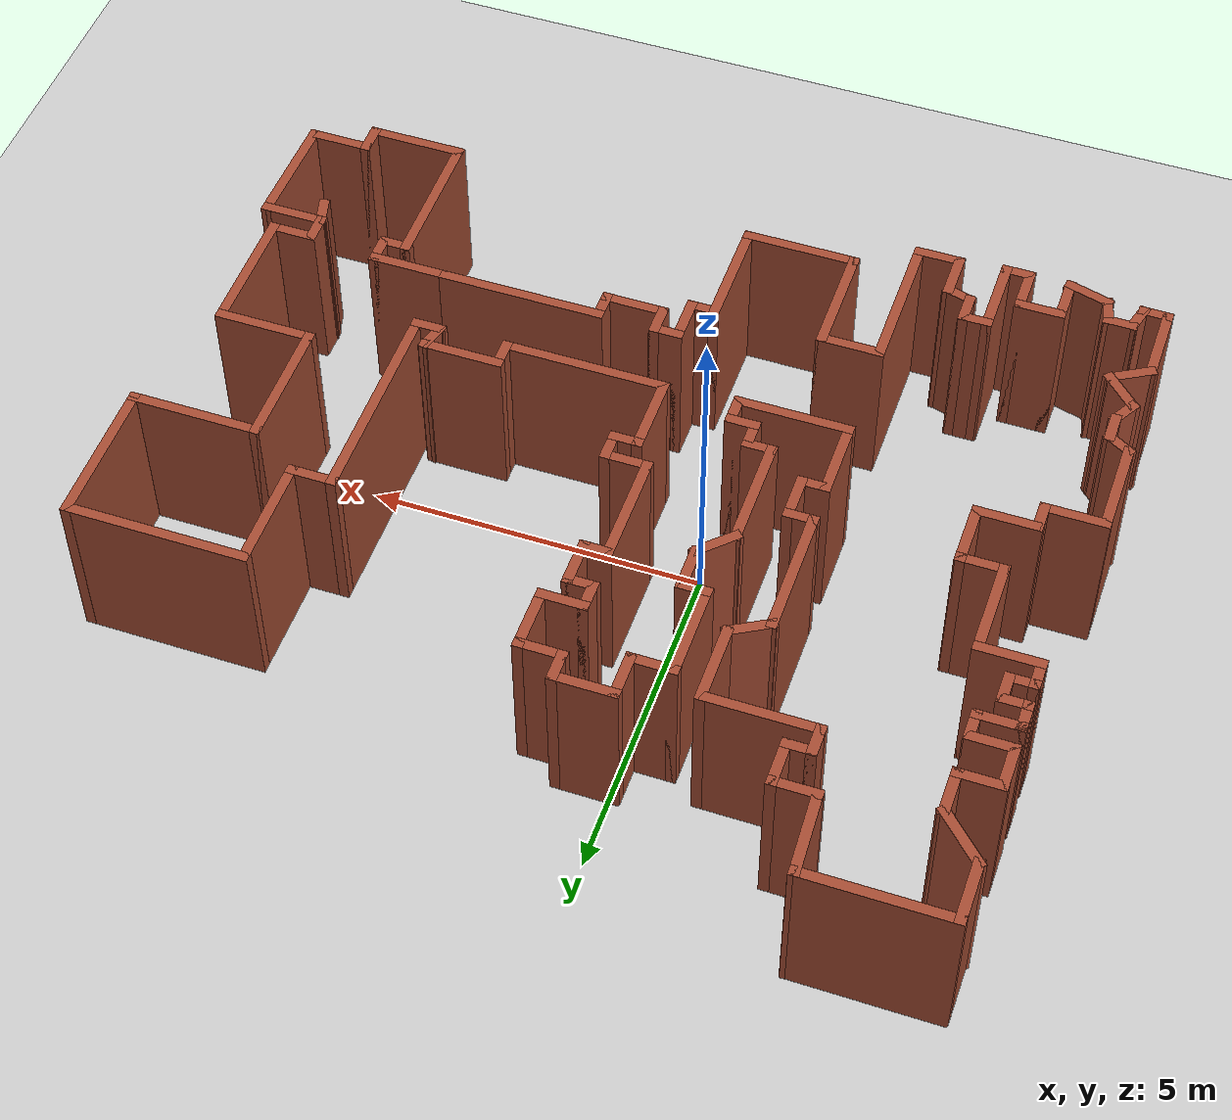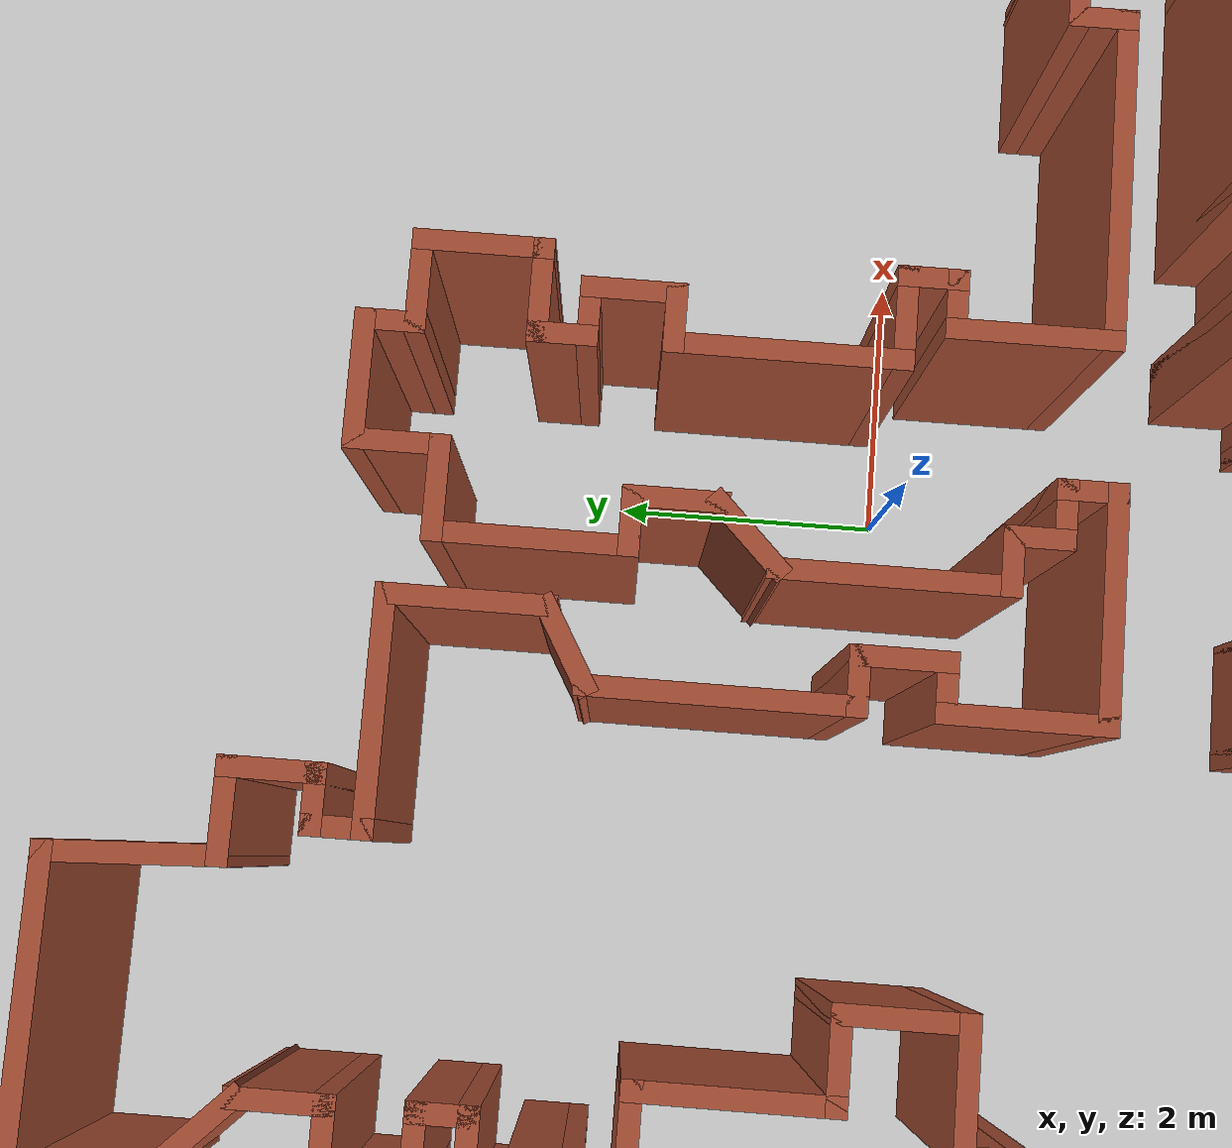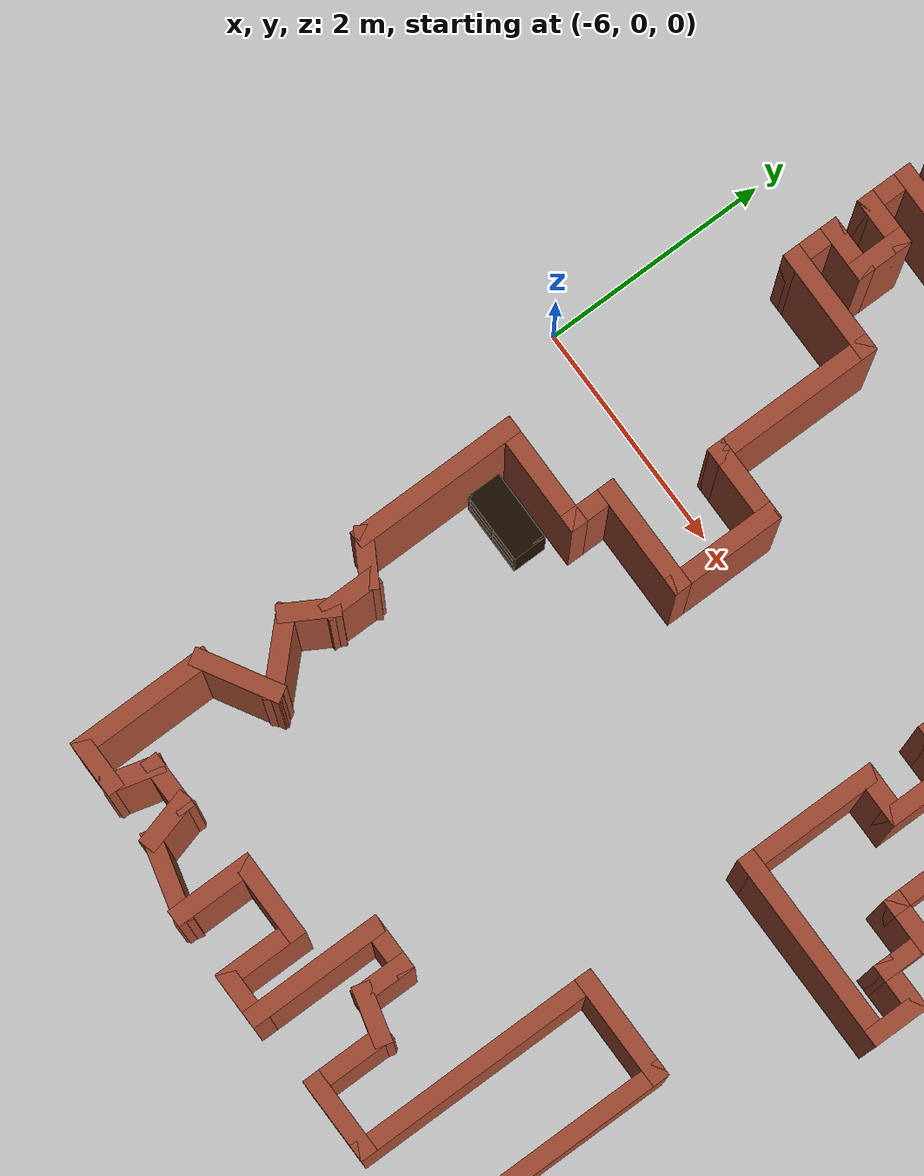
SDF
<sdf version="1.6">
 <world name="default">
  <light name="sun" type="directional">
   <pose>0 0 10 0 -0 0</pose>
   <diffuse>0.8 0.8 0.8 1</diffuse>
   <specular>0.2 0.2 0.2 1</specular>
   <attenuation>
    <range>1000</range>
    <constant>0.9</constant>
    <linear>0.01</linear>
    <quadratic>0.001</quadratic>
   </attenuation>
   <direction>-0.5 0.1 -0.9</direction>
  </light>
  <model name="ground_plane">
   <static>1</static>
   <link name="link">
    <collision name="collision">
     <geometry><plane><normal>0 0 1</normal><size>100 100</size></plane></geometry>
     <surface>
      <contact><collide_bitmask>65535</collide_bitmask></contact>
      <friction><ode><mu>100</mu><mu2>50</mu2></ode></friction>
     </surface>
    </collision>
    <visual name="visual">
     <cast_shadows>0</cast_shadows>
     <geometry><plane><normal>0 0 1</normal><size>100 100</size></plane></geometry>
     <material>
      <script><uri>file://media/materials/scripts/gazebo.material</uri><name>Gazebo/Grey</name></script>
     </material>
    </visual>
   </link>
  </model>
  <gravity>0 0 -9.8</gravity>
  <magnetic_field>6e-06 2.3e-05 -4.2e-05</magnetic_field>
  <atmosphere type="adiabatic"/>
  <physics name="default_physics" default="0" type="ode">
   <max_step_size>0.001</max_step_size>
   <real_time_factor>1</real_time_factor>
   <real_time_update_rate>1000</real_time_update_rate>
  </physics>
  <scene><ambient>0.4 0.4 0.4 1</ambient><background>0.7 0.7 0.7 1</background><shadows>1</shadows></scene>
  <audio><device>default</device></audio>
  <spherical_coordinates>
   <surface_model>EARTH_WGS84</surface_model>
   <latitude_deg>0</latitude_deg>
   <longitude_deg>0</longitude_deg>
   <elevation>0</elevation>
   <heading_deg>0</heading_deg>
  </spherical_coordinates>
  <model name="map_59">
   <pose>1.25432 0.29643 0 0 -0 0</pose>
   <link name="Wall_0">
    <collision name="Wall_0_Collision">
     <geometry><box><size>2.25 0.15 2.5</size></box></geometry>
     <pose>0 0 1.25 0 -0 0</pose>
    </collision>
    <visual name="Wall_0_Visual">
     <pose>0 0 1.25 0 -0 0</pose>
     <geometry><box><size>2.25 0.15 2.5</size></box></geometry>
     <material>
      <script><uri>file://media/materials/scripts/gazebo.material</uri><name>Gazebo/Bricks</name></script>
      <ambient>1 1 1 1</ambient>
     </material>
     <meta><layer>0</layer></meta>
    </visual>
    <pose>-5.34713 5.38602 0 0 -0 3.14159</pose>
   </link>
   <link name="Wall_1">
    <collision name="Wall_1_Collision">
     <geometry><box><size>1 0.15 2.5</size></box></geometry>
     <pose>0 0 1.25 0 -0 0</pose>
    </collision>
    <visual name="Wall_1_Visual">
     <pose>0 0 1.25 0 -0 0</pose>
     <geometry><box><size>1 0.15 2.5</size></box></geometry>
     <material>
      <script><uri>file://media/materials/scripts/gazebo.material</uri><name>Gazebo/Bricks</name></script>
      <ambient>1 1 1 1</ambient>
     </material>
     <meta><layer>0</layer></meta>
    </visual>
    <pose>-6.39713 4.96102 0 0 -0 -1.5708</pose>
   </link>
   <link name="Wall_103">
    <collision name="Wall_103_Collision">
     <geometry><box><size>1 0.15 2.5</size></box></geometry>
     <pose>0 0 1.25 0 -0 0</pose>
    </collision>
    <visual name="Wall_103_Visual">
     <pose>0 0 1.25 0 -0 0</pose>
     <geometry><box><size>1 0.15 2.5</size></box></geometry>
     <material>
      <script><uri>file://media/materials/scripts/gazebo.material</uri><name>Gazebo/Bricks</name></script>
      <ambient>1 1 1 1</ambient>
     </material>
     <meta><layer>0</layer></meta>
    </visual>
    <pose>5.99854 -3.05386 0 0 -0 3.14159</pose>
   </link>
   <link name="Wall_104">
    <collision name="Wall_104_Collision">
     <geometry><box><size>0.5 0.15 2.5</size></box></geometry>
     <pose>0 0 1.25 0 -0 0</pose>
    </collision>
    <visual name="Wall_104_Visual">
     <pose>0 0 1.25 0 -0 0</pose>
     <geometry><box><size>0.5 0.15 2.5</size></box></geometry>
     <material>
      <script><uri>file://media/materials/scripts/gazebo.material</uri><name>Gazebo/Bricks</name></script>
      <ambient>1 1 1 1</ambient>
     </material>
     <meta><layer>0</layer></meta>
    </visual>
    <pose>5.57354 -2.87886 0 0 -0 1.5708</pose>
   </link>
   <link name="Wall_105">
    <collision name="Wall_105_Collision">
     <geometry><box><size>0.75 0.15 2.5</size></box></geometry>
     <pose>0 0 1.25 0 -0 0</pose>
    </collision>
    <visual name="Wall_105_Visual">
     <pose>0 0 1.25 0 -0 0</pose>
     <geometry><box><size>0.75 0.15 2.5</size></box></geometry>
     <material>
      <script><uri>file://media/materials/scripts/gazebo.material</uri><name>Gazebo/Bricks</name></script>
      <ambient>1 1 1 1</ambient>
     </material>
     <meta><layer>0</layer></meta>
    </visual>
    <pose>5.87354 -2.70386 0 0 -0 0</pose>
   </link>
   <link name="Wall_108">
    <collision name="Wall_108_Collision">
     <geometry><box><size>0.5 0.15 2.5</size></box></geometry>
     <pose>0 0 1.25 0 -0 0</pose>
    </collision>
    <visual name="Wall_108_Visual">
     <pose>0 0 1.25 0 -0 0</pose>
     <geometry><box><size>0.5 0.15 2.5</size></box></geometry>
     <material>
      <script><uri>file://media/materials/scripts/gazebo.material</uri><name>Gazebo/Bricks</name></script>
      <ambient>1 1 1 1</ambient>
     </material>
     <meta><layer>0</layer></meta>
    </visual>
    <pose>5.61884 -3.22289 0 0 -0 -1.309</pose>
   </link>
   <link name="Wall_114">
    <collision name="Wall_114_Collision">
     <geometry><box><size>1.5 0.15 2.5</size></box></geometry>
     <pose>0 0 1.25 0 -0 0</pose>
    </collision>
    <visual name="Wall_114_Visual">
     <pose>0 0 1.25 0 -0 0</pose>
     <geometry><box><size>1.5 0.15 2.5</size></box></geometry>
     <material>
      <script><uri>file://media/materials/scripts/gazebo.material</uri><name>Gazebo/Bricks</name></script>
      <ambient>1 1 1 1</ambient>
     </material>
     <meta><layer>0</layer></meta>
    </visual>
    <pose>4.86047 -5.06327 0 0 -0 0</pose>
   </link>
   <link name="Wall_115">
    <collision name="Wall_115_Collision">
     <geometry><box><size>0.5 0.15 2.5</size></box></geometry>
     <pose>0 0 1.25 0 -0 0</pose>
    </collision>
    <visual name="Wall_115_Visual">
     <pose>0 0 1.25 0 -0 0</pose>
     <geometry><box><size>0.5 0.15 2.5</size></box></geometry>
     <material>
      <script><uri>file://media/materials/scripts/gazebo.material</uri><name>Gazebo/Bricks</name></script>
      <ambient>1 1 1 1</ambient>
     </material>
     <meta><layer>0</layer></meta>
    </visual>
    <pose>5.53547 -4.88827 0 0 -0 1.5708</pose>
   </link>
   <link name="Wall_118">
    <collision name="Wall_118_Collision">
     <geometry><box><size>1 0.15 2.5</size></box></geometry>
     <pose>0 0 1.25 0 -0 0</pose>
    </collision>
    <visual name="Wall_118_Visual">
     <pose>0 0 1.25 0 -0 0</pose>
     <geometry><box><size>1 0.15 2.5</size></box></geometry>
     <material>
      <script><uri>file://media/materials/scripts/gazebo.material</uri><name>Gazebo/Bricks</name></script>
      <ambient>1 1 1 1</ambient>
     </material>
     <meta><layer>0</layer></meta>
    </visual>
    <pose>5.96047 -4.71327 0 0 -0 0</pose>
   </link>
   <link name="Wall_119">
    <collision name="Wall_119_Collision">
     <geometry><box><size>1.80985 0.15 2.5</size></box></geometry>
     <pose>0 0 1.25 0 -0 0</pose>
    </collision>
    <visual name="Wall_119_Visual">
     <pose>0 0 1.25 0 -0 0</pose>
     <geometry><box><size>1.80985 0.15 2.5</size></box></geometry>
     <material>
      <script><uri>file://media/materials/scripts/gazebo.material</uri><name>Gazebo/Bricks</name></script>
      <ambient>1 1 1 1</ambient>
     </material>
     <meta><layer>0</layer></meta>
    </visual>
    <pose>6.40451 -3.88356 0 0 -0 1.54786</pose>
   </link>
   <link name="Wall_121">
    <collision name="Wall_121_Collision">
     <geometry><box><size>2 0.15 2.5</size></box></geometry>
     <pose>0 0 1.25 0 -0 0</pose>
    </collision>
    <visual name="Wall_121_Visual">
     <pose>0 0 1.25 0 -0 0</pose>
     <geometry><box><size>2 0.15 2.5</size></box></geometry>
     <material>
      <script><uri>file://media/materials/scripts/gazebo.material</uri><name>Gazebo/Bricks</name></script>
      <ambient>1 1 1 1</ambient>
     </material>
     <meta><layer>0</layer></meta>
    </visual>
    <pose>4.82354 0.071143 0 0 -0 1.5708</pose>
   </link>
   <link name="Wall_122">
    <collision name="Wall_122_Collision">
     <geometry><box><size>2 0.15 2.5</size></box></geometry>
     <pose>0 0 1.25 0 -0 0</pose>
    </collision>
    <visual name="Wall_122_Visual">
     <pose>0 0 1.25 0 -0 0</pose>
     <geometry><box><size>2 0.15 2.5</size></box></geometry>
     <material>
      <script><uri>file://media/materials/scripts/gazebo.material</uri><name>Gazebo/Bricks</name></script>
      <ambient>1 1 1 1</ambient>
     </material>
     <meta><layer>0</layer></meta>
    </visual>
    <pose>5.74854 0.996143 0 0 -0 0</pose>
   </link>
   <link name="Wall_123">
    <collision name="Wall_123_Collision">
     <geometry><box><size>2.25 0.15 2.5</size></box></geometry>
     <pose>0 0 1.25 0 -0 0</pose>
    </collision>
    <visual name="Wall_123_Visual">
     <pose>0 0 1.25 0 -0 0</pose>
     <geometry><box><size>2.25 0.15 2.5</size></box></geometry>
     <material>
      <script><uri>file://media/materials/scripts/gazebo.material</uri><name>Gazebo/Bricks</name></script>
      <ambient>1 1 1 1</ambient>
     </material>
     <meta><layer>0</layer></meta>
    </visual>
    <pose>6.67354 2.04614 0 0 -0 1.5708</pose>
   </link>
   <link name="Wall_124">
    <collision name="Wall_124_Collision">
     <geometry><box><size>2.75 0.15 2.5</size></box></geometry>
     <pose>0 0 1.25 0 -0 0</pose>
    </collision>
    <visual name="Wall_124_Visual">
     <pose>0 0 1.25 0 -0 0</pose>
     <geometry><box><size>2.75 0.15 2.5</size></box></geometry>
     <material>
      <script><uri>file://media/materials/scripts/gazebo.material</uri><name>Gazebo/Bricks</name></script>
      <ambient>1 1 1 1</ambient>
     </material>
     <meta><layer>0</layer></meta>
    </visual>
    <pose>5.37354 3.09614 0 0 -0 3.14159</pose>
   </link>
   <link name="Wall_125">
    <collision name="Wall_125_Collision">
     <geometry><box><size>1.75 0.15 2.5</size></box></geometry>
     <pose>0 0 1.25 0 -0 0</pose>
    </collision>
    <visual name="Wall_125_Visual">
     <pose>0 0 1.25 0 -0 0</pose>
     <geometry><box><size>1.75 0.15 2.5</size></box></geometry>
     <material>
      <script><uri>file://media/materials/scripts/gazebo.material</uri><name>Gazebo/Bricks</name></script>
      <ambient>1 1 1 1</ambient>
     </material>
     <meta><layer>0</layer></meta>
    </visual>
    <pose>4.07354 2.29614 0 0 -0 -1.5708</pose>
   </link>
   <link name="Wall_126">
    <collision name="Wall_126_Collision">
     <geometry><box><size>0.75 0.15 2.5</size></box></geometry>
     <pose>0 0 1.25 0 -0 0</pose>
    </collision>
    <visual name="Wall_126_Visual">
     <pose>0 0 1.25 0 -0 0</pose>
     <geometry><box><size>0.75 0.15 2.5</size></box></geometry>
     <material>
      <script><uri>file://media/materials/scripts/gazebo.material</uri><name>Gazebo/Bricks</name></script>
      <ambient>1 1 1 1</ambient>
     </material>
     <meta><layer>0</layer></meta>
    </visual>
    <pose>3.77354 1.49614 0 0 -0 3.14159</pose>
   </link>
   <link name="Wall_127">
    <collision name="Wall_127_Collision">
     <geometry><box><size>3.25 0.15 2.5</size></box></geometry>
     <pose>0 0 1.25 0 -0 0</pose>
    </collision>
    <visual name="Wall_127_Visual">
     <pose>0 0 1.25 0 -0 0</pose>
     <geometry><box><size>3.25 0.15 2.5</size></box></geometry>
     <material>
      <script><uri>file://media/materials/scripts/gazebo.material</uri><name>Gazebo/Bricks</name></script>
      <ambient>1 1 1 1</ambient>
     </material>
     <meta><layer>0</layer></meta>
    </visual>
    <pose>3.47354 -0.053857 0 0 -0 -1.5708</pose>
   </link>
   <link name="Wall_128">
    <collision name="Wall_128_Collision">
     <geometry><box><size>0.5 0.15 2.5</size></box></geometry>
     <pose>0 0 1.25 0 -0 0</pose>
    </collision>
    <visual name="Wall_128_Visual">
     <pose>0 0 1.25 0 -0 0</pose>
     <geometry><box><size>0.5 0.15 2.5</size></box></geometry>
     <material>
      <script><uri>file://media/materials/scripts/gazebo.material</uri><name>Gazebo/Bricks</name></script>
      <ambient>1 1 1 1</ambient>
     </material>
     <meta><layer>0</layer></meta>
    </visual>
    <pose>3.29854 -1.60386 0 0 -0 3.14159</pose>
   </link>
   <link name="Wall_129">
    <collision name="Wall_129_Collision">
     <geometry><box><size>0.5 0.15 2.5</size></box></geometry>
     <pose>0 0 1.25 0 -0 0</pose>
    </collision>
    <visual name="Wall_129_Visual">
     <pose>0 0 1.25 0 -0 0</pose>
     <geometry><box><size>0.5 0.15 2.5</size></box></geometry>
     <material>
      <script><uri>file://media/materials/scripts/gazebo.material</uri><name>Gazebo/Bricks</name></script>
      <ambient>1 1 1 1</ambient>
     </material>
     <meta><layer>0</layer></meta>
    </visual>
    <pose>3.16884 -1.43482 0 0 -0 1.309</pose>
   </link>
   <link name="Wall_130">
    <collision name="Wall_130_Collision">
     <geometry><box><size>1.25 0.15 2.5</size></box></geometry>
     <pose>0 0 1.25 0 -0 0</pose>
    </collision>
    <visual name="Wall_130_Visual">
     <pose>0 0 1.25 0 -0 0</pose>
     <geometry><box><size>1.25 0.15 2.5</size></box></geometry>
     <material>
      <script><uri>file://media/materials/scripts/gazebo.material</uri><name>Gazebo/Bricks</name></script>
      <ambient>1 1 1 1</ambient>
     </material>
     <meta><layer>0</layer></meta>
    </visual>
    <pose>2.66413 -1.26578 0 0 -0 3.14159</pose>
   </link>
   <link name="Wall_131">
    <collision name="Wall_131_Collision">
     <geometry><box><size>0.5 0.15 2.5</size></box></geometry>
     <pose>0 0 1.25 0 -0 0</pose>
    </collision>
    <visual name="Wall_131_Visual">
     <pose>0 0 1.25 0 -0 0</pose>
     <geometry><box><size>0.5 0.15 2.5</size></box></geometry>
     <material>
      <script><uri>file://media/materials/scripts/gazebo.material</uri><name>Gazebo/Bricks</name></script>
      <ambient>1 1 1 1</ambient>
     </material>
     <meta><layer>0</layer></meta>
    </visual>
    <pose>2.11413 -1.44078 0 0 -0 -1.5708</pose>
   </link>
   <link name="Wall_132">
    <collision name="Wall_132_Collision">
     <geometry><box><size>2.5 0.15 2.5</size></box></geometry>
     <pose>0 0 1.25 0 -0 0</pose>
    </collision>
    <visual name="Wall_132_Visual">
     <pose>0 0 1.25 0 -0 0</pose>
     <geometry><box><size>2.5 0.15 2.5</size></box></geometry>
     <material>
      <script><uri>file://media/materials/scripts/gazebo.material</uri><name>Gazebo/Bricks</name></script>
      <ambient>1 1 1 1</ambient>
     </material>
     <meta><layer>0</layer></meta>
    </visual>
    <pose>0.93913 -1.61578 0 0 -0 3.14159</pose>
   </link>
   <link name="Wall_133">
    <collision name="Wall_133_Collision">
     <geometry><box><size>1.25 0.15 2.5</size></box></geometry>
     <pose>0 0 1.25 0 -0 0</pose>
    </collision>
    <visual name="Wall_133_Visual">
     <pose>0 0 1.25 0 -0 0</pose>
     <geometry><box><size>1.25 0.15 2.5</size></box></geometry>
     <material>
      <script><uri>file://media/materials/scripts/gazebo.material</uri><name>Gazebo/Bricks</name></script>
      <ambient>1 1 1 1</ambient>
     </material>
     <meta><layer>0</layer></meta>
    </visual>
    <pose>-0.23587 -1.06578 0 0 -0 1.5708</pose>
   </link>
   <link name="Wall_134">
    <collision name="Wall_134_Collision">
     <geometry><box><size>0.5 0.15 2.5</size></box></geometry>
     <pose>0 0 1.25 0 -0 0</pose>
    </collision>
    <visual name="Wall_134_Visual">
     <pose>0 0 1.25 0 -0 0</pose>
     <geometry><box><size>0.5 0.15 2.5</size></box></geometry>
     <material>
      <script><uri>file://media/materials/scripts/gazebo.material</uri><name>Gazebo/Bricks</name></script>
      <ambient>1 1 1 1</ambient>
     </material>
     <meta><layer>0</layer></meta>
    </visual>
    <pose>-0.06087 -0.515783 0 0 -0 0</pose>
   </link>
   <link name="Wall_135">
    <collision name="Wall_135_Collision">
     <geometry><box><size>0.5 0.15 2.5</size></box></geometry>
     <pose>0 0 1.25 0 -0 0</pose>
    </collision>
    <visual name="Wall_135_Visual">
     <pose>0 0 1.25 0 -0 0</pose>
     <geometry><box><size>0.5 0.15 2.5</size></box></geometry>
     <material>
      <script><uri>file://media/materials/scripts/gazebo.material</uri><name>Gazebo/Bricks</name></script>
      <ambient>1 1 1 1</ambient>
     </material>
     <meta><layer>0</layer></meta>
    </visual>
    <pose>0.11413 -0.340783 0 0 -0 1.5708</pose>
   </link>
   <link name="Wall_136">
    <collision name="Wall_136_Collision">
     <geometry><box><size>0.75 0.15 2.5</size></box></geometry>
     <pose>0 0 1.25 0 -0 0</pose>
    </collision>
    <visual name="Wall_136_Visual">
     <pose>0 0 1.25 0 -0 0</pose>
     <geometry><box><size>0.75 0.15 2.5</size></box></geometry>
     <material>
      <script><uri>file://media/materials/scripts/gazebo.material</uri><name>Gazebo/Bricks</name></script>
      <ambient>1 1 1 1</ambient>
     </material>
     <meta><layer>0</layer></meta>
    </visual>
    <pose>-0.18587 -0.165783 0 0 -0 3.14159</pose>
   </link>
   <link name="Wall_139">
    <collision name="Wall_139_Collision">
     <geometry><box><size>1.75 0.15 2.5</size></box></geometry>
     <pose>0 0 1.25 0 -0 0</pose>
    </collision>
    <visual name="Wall_139_Visual">
     <pose>0 0 1.25 0 -0 0</pose>
     <geometry><box><size>1.75 0.15 2.5</size></box></geometry>
     <material>
      <script><uri>file://media/materials/scripts/gazebo.material</uri><name>Gazebo/Bricks</name></script>
      <ambient>1 1 1 1</ambient>
     </material>
     <meta><layer>0</layer></meta>
    </visual>
    <pose>-0.48587 0.634217 0 0 -0 1.5708</pose>
   </link>
   <link name="Wall_140">
    <collision name="Wall_140_Collision">
     <geometry><box><size>0.5 0.15 2.5</size></box></geometry>
     <pose>0 0 1.25 0 -0 0</pose>
    </collision>
    <visual name="Wall_140_Visual">
     <pose>0 0 1.25 0 -0 0</pose>
     <geometry><box><size>0.5 0.15 2.5</size></box></geometry>
     <material>
      <script><uri>file://media/materials/scripts/gazebo.material</uri><name>Gazebo/Bricks</name></script>
      <ambient>1 1 1 1</ambient>
     </material>
     <meta><layer>0</layer></meta>
    </visual>
    <pose>-0.31087 1.43422 0 0 -0 0</pose>
   </link>
   <link name="Wall_143">
    <collision name="Wall_143_Collision">
     <geometry><box><size>0.75 0.15 2.5</size></box></geometry>
     <pose>0 0 1.25 0 -0 0</pose>
    </collision>
    <visual name="Wall_143_Visual">
     <pose>0 0 1.25 0 -0 0</pose>
     <geometry><box><size>0.75 0.15 2.5</size></box></geometry>
     <material>
      <script><uri>file://media/materials/scripts/gazebo.material</uri><name>Gazebo/Bricks</name></script>
      <ambient>1 1 1 1</ambient>
     </material>
     <meta><layer>0</layer></meta>
    </visual>
    <pose>-0.13587 1.73422 0 0 -0 1.5708</pose>
   </link>
   <link name="Wall_144">
    <collision name="Wall_144_Collision">
     <geometry><box><size>0.5 0.15 2.5</size></box></geometry>
     <pose>0 0 1.25 0 -0 0</pose>
    </collision>
    <visual name="Wall_144_Visual">
     <pose>0 0 1.25 0 -0 0</pose>
     <geometry><box><size>0.5 0.15 2.5</size></box></geometry>
     <material>
      <script><uri>file://media/materials/scripts/gazebo.material</uri><name>Gazebo/Bricks</name></script>
      <ambient>1 1 1 1</ambient>
     </material>
     <meta><layer>0</layer></meta>
    </visual>
    <pose>-0.31087 2.03422 0 0 -0 3.14159</pose>
   </link>
   <link name="Wall_145">
    <collision name="Wall_145_Collision">
     <geometry><box><size>0.5 0.15 2.5</size></box></geometry>
     <pose>0 0 1.25 0 -0 0</pose>
    </collision>
    <visual name="Wall_145_Visual">
     <pose>0 0 1.25 0 -0 0</pose>
     <geometry><box><size>0.5 0.15 2.5</size></box></geometry>
     <material>
      <script><uri>file://media/materials/scripts/gazebo.material</uri><name>Gazebo/Bricks</name></script>
      <ambient>1 1 1 1</ambient>
     </material>
     <meta><layer>0</layer></meta>
    </visual>
    <pose>-0.48587 2.20922 0 0 -0 1.5708</pose>
   </link>
   <link name="Wall_146">
    <collision name="Wall_146_Collision">
     <geometry><box><size>0.75 0.15 2.5</size></box></geometry>
     <pose>0 0 1.25 0 -0 0</pose>
    </collision>
    <visual name="Wall_146_Visual">
     <pose>0 0 1.25 0 -0 0</pose>
     <geometry><box><size>0.75 0.15 2.5</size></box></geometry>
     <material>
      <script><uri>file://media/materials/scripts/gazebo.material</uri><name>Gazebo/Bricks</name></script>
      <ambient>1 1 1 1</ambient>
     </material>
     <meta><layer>0</layer></meta>
    </visual>
    <pose>-0.18587 2.38422 0 0 -0 0</pose>
   </link>
   <link name="Wall_147">
    <collision name="Wall_147_Collision">
     <geometry><box><size>1 0.15 2.5</size></box></geometry>
     <pose>0 0 1.25 0 -0 0</pose>
    </collision>
    <visual name="Wall_147_Visual">
     <pose>0 0 1.25 0 -0 0</pose>
     <geometry><box><size>1 0.15 2.5</size></box></geometry>
     <material>
      <script><uri>file://media/materials/scripts/gazebo.material</uri><name>Gazebo/Bricks</name></script>
      <ambient>1 1 1 1</ambient>
     </material>
     <meta><layer>0</layer></meta>
    </visual>
    <pose>0.11413 2.80922 0 0 -0 1.5708</pose>
   </link>
   <link name="Wall_148">
    <collision name="Wall_148_Collision">
     <geometry><box><size>0.75 0.15 2.5</size></box></geometry>
     <pose>0 0 1.25 0 -0 0</pose>
    </collision>
    <visual name="Wall_148_Visual">
     <pose>0 0 1.25 0 -0 0</pose>
     <geometry><box><size>0.75 0.15 2.5</size></box></geometry>
     <material>
      <script><uri>file://media/materials/scripts/gazebo.material</uri><name>Gazebo/Bricks</name></script>
      <ambient>1 1 1 1</ambient>
     </material>
     <meta><layer>0</layer></meta>
    </visual>
    <pose>-0.18587 3.23422 0 0 -0 3.14159</pose>
   </link>
   <link name="Wall_149">
    <collision name="Wall_149_Collision">
     <geometry><box><size>0.5 0.15 2.5</size></box></geometry>
     <pose>0 0 1.25 0 -0 0</pose>
    </collision>
    <visual name="Wall_149_Visual">
     <pose>0 0 1.25 0 -0 0</pose>
     <geometry><box><size>0.5 0.15 2.5</size></box></geometry>
     <material>
      <script><uri>file://media/materials/scripts/gazebo.material</uri><name>Gazebo/Bricks</name></script>
      <ambient>1 1 1 1</ambient>
     </material>
     <meta><layer>0</layer></meta>
    </visual>
    <pose>-0.48587 3.40922 0 0 -0 1.5708</pose>
   </link>
   <link name="Wall_150">
    <collision name="Wall_150_Collision">
     <geometry><box><size>1 0.15 2.5</size></box></geometry>
     <pose>0 0 1.25 0 -0 0</pose>
    </collision>
    <visual name="Wall_150_Visual">
     <pose>0 0 1.25 0 -0 0</pose>
     <geometry><box><size>1 0.15 2.5</size></box></geometry>
     <material>
      <script><uri>file://media/materials/scripts/gazebo.material</uri><name>Gazebo/Bricks</name></script>
      <ambient>1 1 1 1</ambient>
     </material>
     <meta><layer>0</layer></meta>
    </visual>
    <pose>-0.91087 3.58422 0 0 -0 3.14159</pose>
   </link>
   <link name="Wall_151">
    <collision name="Wall_151_Collision">
     <geometry><box><size>0.75 0.15 2.5</size></box></geometry>
     <pose>0 0 1.25 0 -0 0</pose>
    </collision>
    <visual name="Wall_151_Visual">
     <pose>0 0 1.25 0 -0 0</pose>
     <geometry><box><size>0.75 0.15 2.5</size></box></geometry>
     <material>
      <script><uri>file://media/materials/scripts/gazebo.material</uri><name>Gazebo/Bricks</name></script>
      <ambient>1 1 1 1</ambient>
     </material>
     <meta><layer>0</layer></meta>
    </visual>
    <pose>-1.33587 3.28422 0 0 -0 -1.5708</pose>
   </link>
   <link name="Wall_152">
    <collision name="Wall_152_Collision">
     <geometry><box><size>0.75 0.15 2.5</size></box></geometry>
     <pose>0 0 1.25 0 -0 0</pose>
    </collision>
    <visual name="Wall_152_Visual">
     <pose>0 0 1.25 0 -0 0</pose>
     <geometry><box><size>0.75 0.15 2.5</size></box></geometry>
     <material>
      <script><uri>file://media/materials/scripts/gazebo.material</uri><name>Gazebo/Bricks</name></script>
      <ambient>1 1 1 1</ambient>
     </material>
     <meta><layer>0</layer></meta>
    </visual>
    <pose>-1.63587 2.98422 0 0 -0 3.14159</pose>
   </link>
   <link name="Wall_153">
    <collision name="Wall_153_Collision">
     <geometry><box><size>1.5 0.15 2.5</size></box></geometry>
     <pose>0 0 1.25 0 -0 0</pose>
    </collision>
    <visual name="Wall_153_Visual">
     <pose>0 0 1.25 0 -0 0</pose>
     <geometry><box><size>1.5 0.15 2.5</size></box></geometry>
     <material>
      <script><uri>file://media/materials/scripts/gazebo.material</uri><name>Gazebo/Bricks</name></script>
      <ambient>1 1 1 1</ambient>
     </material>
     <meta><layer>0</layer></meta>
    </visual>
    <pose>-1.93587 2.30922 0 0 -0 -1.5708</pose>
   </link>
   <link name="Wall_154">
    <collision name="Wall_154_Collision">
     <geometry><box><size>0.5 0.15 2.5</size></box></geometry>
     <pose>0 0 1.25 0 -0 0</pose>
    </collision>
    <visual name="Wall_154_Visual">
     <pose>0 0 1.25 0 -0 0</pose>
     <geometry><box><size>0.5 0.15 2.5</size></box></geometry>
     <material>
      <script><uri>file://media/materials/scripts/gazebo.material</uri><name>Gazebo/Bricks</name></script>
      <ambient>1 1 1 1</ambient>
     </material>
     <meta><layer>0</layer></meta>
    </visual>
    <pose>-1.76087 1.63422 0 0 -0 0</pose>
   </link>
   <link name="Wall_155">
    <collision name="Wall_155_Collision">
     <geometry><box><size>0.75 0.15 2.5</size></box></geometry>
     <pose>0 0 1.25 0 -0 0</pose>
    </collision>
    <visual name="Wall_155_Visual">
     <pose>0 0 1.25 0 -0 0</pose>
     <geometry><box><size>0.75 0.15 2.5</size></box></geometry>
     <material>
      <script><uri>file://media/materials/scripts/gazebo.material</uri><name>Gazebo/Bricks</name></script>
      <ambient>1 1 1 1</ambient>
     </material>
     <meta><layer>0</layer></meta>
    </visual>
    <pose>-1.58587 1.33422 0 0 -0 -1.5708</pose>
   </link>
   <link name="Wall_156">
    <collision name="Wall_156_Collision">
     <geometry><box><size>0.75 0.15 2.5</size></box></geometry>
     <pose>0 0 1.25 0 -0 0</pose>
    </collision>
    <visual name="Wall_156_Visual">
     <pose>0 0 1.25 0 -0 0</pose>
     <geometry><box><size>0.75 0.15 2.5</size></box></geometry>
     <material>
      <script><uri>file://media/materials/scripts/gazebo.material</uri><name>Gazebo/Bricks</name></script>
      <ambient>1 1 1 1</ambient>
     </material>
     <meta><layer>0</layer></meta>
    </visual>
    <pose>-1.798 0.822085 0 0 -0 -2.35619</pose>
   </link>
   <link name="Wall_160">
    <collision name="Wall_160_Collision">
     <geometry><box><size>1.75 0.15 2.5</size></box></geometry>
     <pose>0 0 1.25 0 -0 0</pose>
    </collision>
    <visual name="Wall_160_Visual">
     <pose>0 0 1.25 0 -0 0</pose>
     <geometry><box><size>1.75 0.15 2.5</size></box></geometry>
     <material>
      <script><uri>file://media/materials/scripts/gazebo.material</uri><name>Gazebo/Bricks</name></script>
      <ambient>1 1 1 1</ambient>
     </material>
     <meta><layer>0</layer></meta>
    </visual>
    <pose>-2.01013 -0.190047 0 0 -0 -1.5708</pose>
   </link>
   <link name="Wall_161">
    <collision name="Wall_161_Collision">
     <geometry><box><size>0.5 0.15 2.5</size></box></geometry>
     <pose>0 0 1.25 0 -0 0</pose>
    </collision>
    <visual name="Wall_161_Visual">
     <pose>0 0 1.25 0 -0 0</pose>
     <geometry><box><size>0.5 0.15 2.5</size></box></geometry>
     <material>
      <script><uri>file://media/materials/scripts/gazebo.material</uri><name>Gazebo/Bricks</name></script>
      <ambient>1 1 1 1</ambient>
     </material>
     <meta><layer>0</layer></meta>
    </visual>
    <pose>-1.83513 -0.990047 0 0 -0 0</pose>
   </link>
   <link name="Wall_162">
    <collision name="Wall_162_Collision">
     <geometry><box><size>0.5 0.15 2.5</size></box></geometry>
     <pose>0 0 1.25 0 -0 0</pose>
    </collision>
    <visual name="Wall_162_Visual">
     <pose>0 0 1.25 0 -0 0</pose>
     <geometry><box><size>0.5 0.15 2.5</size></box></geometry>
     <material>
      <script><uri>file://media/materials/scripts/gazebo.material</uri><name>Gazebo/Bricks</name></script>
      <ambient>1 1 1 1</ambient>
     </material>
     <meta><layer>0</layer></meta>
    </visual>
    <pose>-1.66013 -1.16505 0 0 -0 -1.5708</pose>
   </link>
   <link name="Wall_163">
    <collision name="Wall_163_Collision">
     <geometry><box><size>0.5 0.15 2.5</size></box></geometry>
     <pose>0 0 1.25 0 -0 0</pose>
    </collision>
    <visual name="Wall_163_Visual">
     <pose>0 0 1.25 0 -0 0</pose>
     <geometry><box><size>0.5 0.15 2.5</size></box></geometry>
     <material>
      <script><uri>file://media/materials/scripts/gazebo.material</uri><name>Gazebo/Bricks</name></script>
      <ambient>1 1 1 1</ambient>
     </material>
     <meta><layer>0</layer></meta>
    </visual>
    <pose>-1.48513 -1.34005 0 0 -0 0</pose>
   </link>
   <link name="Wall_164">
    <collision name="Wall_164_Collision">
     <geometry><box><size>0.5 0.15 2.5</size></box></geometry>
     <pose>0 0 1.25 0 -0 0</pose>
    </collision>
    <visual name="Wall_164_Visual">
     <pose>0 0 1.25 0 -0 0</pose>
     <geometry><box><size>0.5 0.15 2.5</size></box></geometry>
     <material>
      <script><uri>file://media/materials/scripts/gazebo.material</uri><name>Gazebo/Bricks</name></script>
      <ambient>1 1 1 1</ambient>
     </material>
     <meta><layer>0</layer></meta>
    </visual>
    <pose>-1.31013 -1.51505 0 0 -0 -1.5708</pose>
   </link>
   <link name="Wall_165">
    <collision name="Wall_165_Collision">
     <geometry><box><size>1.75 0.15 2.5</size></box></geometry>
     <pose>0 0 1.25 0 -0 0</pose>
    </collision>
    <visual name="Wall_165_Visual">
     <pose>0 0 1.25 0 -0 0</pose>
     <geometry><box><size>1.75 0.15 2.5</size></box></geometry>
     <material>
      <script><uri>file://media/materials/scripts/gazebo.material</uri><name>Gazebo/Bricks</name></script>
      <ambient>1 1 1 1</ambient>
     </material>
     <meta><layer>0</layer></meta>
    </visual>
    <pose>-2.11013 -1.69005 0 0 -0 3.14159</pose>
   </link>
   <link name="Wall_166">
    <collision name="Wall_166_Collision">
     <geometry><box><size>1.25 0.15 2.5</size></box></geometry>
     <pose>0 0 1.25 0 -0 0</pose>
    </collision>
    <visual name="Wall_166_Visual">
     <pose>0 0 1.25 0 -0 0</pose>
     <geometry><box><size>1.25 0.15 2.5</size></box></geometry>
     <material>
      <script><uri>file://media/materials/scripts/gazebo.material</uri><name>Gazebo/Bricks</name></script>
      <ambient>1 1 1 1</ambient>
     </material>
     <meta><layer>0</layer></meta>
    </visual>
    <pose>-2.91013 -1.14005 0 0 -0 1.5708</pose>
   </link>
   <link name="Wall_167">
    <collision name="Wall_167_Collision">
     <geometry><box><size>0.5 0.15 2.5</size></box></geometry>
     <pose>0 0 1.25 0 -0 0</pose>
    </collision>
    <visual name="Wall_167_Visual">
     <pose>0 0 1.25 0 -0 0</pose>
     <geometry><box><size>0.5 0.15 2.5</size></box></geometry>
     <material>
      <script><uri>file://media/materials/scripts/gazebo.material</uri><name>Gazebo/Bricks</name></script>
      <ambient>1 1 1 1</ambient>
     </material>
     <meta><layer>0</layer></meta>
    </visual>
    <pose>-2.73513 -0.590047 0 0 -0 0</pose>
   </link>
   <link name="Wall_168">
    <collision name="Wall_168_Collision">
     <geometry><box><size>0.75 0.15 2.5</size></box></geometry>
     <pose>0 0 1.25 0 -0 0</pose>
    </collision>
    <visual name="Wall_168_Visual">
     <pose>0 0 1.25 0 -0 0</pose>
     <geometry><box><size>0.75 0.15 2.5</size></box></geometry>
     <material>
      <script><uri>file://media/materials/scripts/gazebo.material</uri><name>Gazebo/Bricks</name></script>
      <ambient>1 1 1 1</ambient>
     </material>
     <meta><layer>0</layer></meta>
    </visual>
    <pose>-2.56013 -0.290047 0 0 -0 1.5708</pose>
   </link>
   <link name="Wall_169">
    <collision name="Wall_169_Collision">
     <geometry><box><size>0.5 0.15 2.5</size></box></geometry>
     <pose>0 0 1.25 0 -0 0</pose>
    </collision>
    <visual name="Wall_169_Visual">
     <pose>0 0 1.25 0 -0 0</pose>
     <geometry><box><size>0.5 0.15 2.5</size></box></geometry>
     <material>
      <script><uri>file://media/materials/scripts/gazebo.material</uri><name>Gazebo/Bricks</name></script>
      <ambient>1 1 1 1</ambient>
     </material>
     <meta><layer>0</layer></meta>
    </visual>
    <pose>-2.73513 0.009953 0 0 -0 3.14159</pose>
   </link>
   <link name="Wall_17">
    <collision name="Wall_17_Collision">
     <geometry><box><size>0.5 0.15 2.5</size></box></geometry>
     <pose>0 0 1.25 0 -0 0</pose>
    </collision>
    <visual name="Wall_17_Visual">
     <pose>0 0 1.25 0 -0 0</pose>
     <geometry><box><size>0.5 0.15 2.5</size></box></geometry>
     <material>
      <script><uri>file://media/materials/scripts/gazebo.material</uri><name>Gazebo/Bricks</name></script>
      <ambient>1 1 1 1</ambient>
     </material>
     <meta><layer>0</layer></meta>
    </visual>
    <pose>-6.39609 2.20998 0 0 -0 -1.5708</pose>
   </link>
   <link name="Wall_170">
    <collision name="Wall_170_Collision">
     <geometry><box><size>2 0.15 2.5</size></box></geometry>
     <pose>0 0 1.25 0 -0 0</pose>
    </collision>
    <visual name="Wall_170_Visual">
     <pose>0 0 1.25 0 -0 0</pose>
     <geometry><box><size>2 0.15 2.5</size></box></geometry>
     <material>
      <script><uri>file://media/materials/scripts/gazebo.material</uri><name>Gazebo/Bricks</name></script>
      <ambient>1 1 1 1</ambient>
     </material>
     <meta><layer>0</layer></meta>
    </visual>
    <pose>-2.91013 0.934953 0 0 -0 1.5708</pose>
   </link>
   <link name="Wall_171">
    <collision name="Wall_171_Collision">
     <geometry><box><size>0.75 0.15 2.5</size></box></geometry>
     <pose>0 0 1.25 0 -0 0</pose>
    </collision>
    <visual name="Wall_171_Visual">
     <pose>0 0 1.25 0 -0 0</pose>
     <geometry><box><size>0.75 0.15 2.5</size></box></geometry>
     <material>
      <script><uri>file://media/materials/scripts/gazebo.material</uri><name>Gazebo/Bricks</name></script>
      <ambient>1 1 1 1</ambient>
     </material>
     <meta><layer>0</layer></meta>
    </visual>
    <pose>-2.65033 2.00995 0 0 -0 0.523599</pose>
   </link>
   <link name="Wall_172">
    <collision name="Wall_172_Collision">
     <geometry><box><size>1.25 0.15 2.5</size></box></geometry>
     <pose>0 0 1.25 0 -0 0</pose>
    </collision>
    <visual name="Wall_172_Visual">
     <pose>0 0 1.25 0 -0 0</pose>
     <geometry><box><size>1.25 0.15 2.5</size></box></geometry>
     <material>
      <script><uri>file://media/materials/scripts/gazebo.material</uri><name>Gazebo/Bricks</name></script>
      <ambient>1 1 1 1</ambient>
     </material>
     <meta><layer>0</layer></meta>
    </visual>
    <pose>-2.39052 2.70995 0 0 -0 1.5708</pose>
   </link>
   <link name="Wall_173">
    <collision name="Wall_173_Collision">
     <geometry><box><size>1.75 0.15 2.5</size></box></geometry>
     <pose>0 0 1.25 0 -0 0</pose>
    </collision>
    <visual name="Wall_173_Visual">
     <pose>0 0 1.25 0 -0 0</pose>
     <geometry><box><size>1.75 0.15 2.5</size></box></geometry>
     <material>
      <script><uri>file://media/materials/scripts/gazebo.material</uri><name>Gazebo/Bricks</name></script>
      <ambient>1 1 1 1</ambient>
     </material>
     <meta><layer>0</layer></meta>
    </visual>
    <pose>-3.19052 3.25995 0 0 -0 3.14159</pose>
   </link>
   <link name="Wall_174">
    <collision name="Wall_174_Collision">
     <geometry><box><size>0.5 0.15 2.5</size></box></geometry>
     <pose>0 0 1.25 0 -0 0</pose>
    </collision>
    <visual name="Wall_174_Visual">
     <pose>0 0 1.25 0 -0 0</pose>
     <geometry><box><size>0.5 0.15 2.5</size></box></geometry>
     <material>
      <script><uri>file://media/materials/scripts/gazebo.material</uri><name>Gazebo/Bricks</name></script>
      <ambient>1 1 1 1</ambient>
     </material>
     <meta><layer>0</layer></meta>
    </visual>
    <pose>-3.99052 3.43495 0 0 -0 1.5708</pose>
   </link>
   <link name="Wall_175">
    <collision name="Wall_175_Collision">
     <geometry><box><size>0.5 0.15 2.5</size></box></geometry>
     <pose>0 0 1.25 0 -0 0</pose>
    </collision>
    <visual name="Wall_175_Visual">
     <pose>0 0 1.25 0 -0 0</pose>
     <geometry><box><size>0.5 0.15 2.5</size></box></geometry>
     <material>
      <script><uri>file://media/materials/scripts/gazebo.material</uri><name>Gazebo/Bricks</name></script>
      <ambient>1 1 1 1</ambient>
     </material>
     <meta><layer>0</layer></meta>
    </visual>
    <pose>-3.81552 3.60995 0 0 -0 0</pose>
   </link>
   <link name="Wall_176">
    <collision name="Wall_176_Collision">
     <geometry><box><size>0.75 0.15 2.5</size></box></geometry>
     <pose>0 0 1.25 0 -0 0</pose>
    </collision>
    <visual name="Wall_176_Visual">
     <pose>0 0 1.25 0 -0 0</pose>
     <geometry><box><size>0.75 0.15 2.5</size></box></geometry>
     <material>
      <script><uri>file://media/materials/scripts/gazebo.material</uri><name>Gazebo/Bricks</name></script>
      <ambient>1 1 1 1</ambient>
     </material>
     <meta><layer>0</layer></meta>
    </visual>
    <pose>-3.64052 3.90995 0 0 -0 1.5708</pose>
   </link>
   <link name="Wall_177">
    <collision name="Wall_177_Collision">
     <geometry><box><size>0.75 0.15 2.5</size></box></geometry>
     <pose>0 0 1.25 0 -0 0</pose>
    </collision>
    <visual name="Wall_177_Visual">
     <pose>0 0 1.25 0 -0 0</pose>
     <geometry><box><size>0.75 0.15 2.5</size></box></geometry>
     <material>
      <script><uri>file://media/materials/scripts/gazebo.material</uri><name>Gazebo/Bricks</name></script>
      <ambient>1 1 1 1</ambient>
     </material>
     <meta><layer>0</layer></meta>
    </visual>
    <pose>-3.94052 4.20995 0 0 -0 3.14159</pose>
   </link>
   <link name="Wall_178">
    <collision name="Wall_178_Collision">
     <geometry><box><size>1.32743 0.15 2.5</size></box></geometry>
     <pose>0 0 1.25 0 -0 0</pose>
    </collision>
    <visual name="Wall_178_Visual">
     <pose>0 0 1.25 0 -0 0</pose>
     <geometry><box><size>1.32743 0.15 2.5</size></box></geometry>
     <material>
      <script><uri>file://media/materials/scripts/gazebo.material</uri><name>Gazebo/Bricks</name></script>
      <ambient>1 1 1 1</ambient>
     </material>
     <meta><layer>0</layer></meta>
    </visual>
    <pose>-4.26883 4.79799 0 0 -0 1.6189</pose>
   </link>
   <link name="Wall_18">
    <collision name="Wall_18_Collision">
     <geometry><box><size>0.5 0.15 2.5</size></box></geometry>
     <pose>0 0 1.25 0 -0 0</pose>
    </collision>
    <visual name="Wall_18_Visual">
     <pose>0 0 1.25 0 -0 0</pose>
     <geometry><box><size>0.5 0.15 2.5</size></box></geometry>
     <material>
      <script><uri>file://media/materials/scripts/gazebo.material</uri><name>Gazebo/Bricks</name></script>
      <ambient>1 1 1 1</ambient>
     </material>
     <meta><layer>0</layer></meta>
    </visual>
    <pose>-6.22109 2.03498 0 0 -0 0</pose>
   </link>
   <link name="Wall_19">
    <collision name="Wall_19_Collision">
     <geometry><box><size>0.5 0.15 2.5</size></box></geometry>
     <pose>0 0 1.25 0 -0 0</pose>
    </collision>
    <visual name="Wall_19_Visual">
     <pose>0 0 1.25 0 -0 0</pose>
     <geometry><box><size>0.5 0.15 2.5</size></box></geometry>
     <material>
      <script><uri>file://media/materials/scripts/gazebo.material</uri><name>Gazebo/Bricks</name></script>
      <ambient>1 1 1 1</ambient>
     </material>
     <meta><layer>0</layer></meta>
    </visual>
    <pose>-6.04609 1.85998 0 0 -0 -1.5708</pose>
   </link>
   <link name="Wall_2">
    <collision name="Wall_2_Collision">
     <geometry><box><size>1 0.15 2.5</size></box></geometry>
     <pose>0 0 1.25 0 -0 0</pose>
    </collision>
    <visual name="Wall_2_Visual">
     <pose>0 0 1.25 0 -0 0</pose>
     <geometry><box><size>1 0.15 2.5</size></box></geometry>
     <material>
      <script><uri>file://media/materials/scripts/gazebo.material</uri><name>Gazebo/Bricks</name></script>
      <ambient>1 1 1 1</ambient>
     </material>
     <meta><layer>0</layer></meta>
    </visual>
    <pose>-6.09661 4.2355 0 0 -0 -0.785398</pose>
   </link>
   <link name="Wall_20">
    <collision name="Wall_20_Collision">
     <geometry><box><size>0.5 0.15 2.5</size></box></geometry>
     <pose>0 0 1.25 0 -0 0</pose>
    </collision>
    <visual name="Wall_20_Visual">
     <pose>0 0 1.25 0 -0 0</pose>
     <geometry><box><size>0.5 0.15 2.5</size></box></geometry>
     <material>
      <script><uri>file://media/materials/scripts/gazebo.material</uri><name>Gazebo/Bricks</name></script>
      <ambient>1 1 1 1</ambient>
     </material>
     <meta><layer>0</layer></meta>
    </visual>
    <pose>-6.22109 1.68498 0 0 -0 3.14159</pose>
   </link>
   <link name="Wall_21">
    <collision name="Wall_21_Collision">
     <geometry><box><size>0.5 0.15 2.5</size></box></geometry>
     <pose>0 0 1.25 0 -0 0</pose>
    </collision>
    <visual name="Wall_21_Visual">
     <pose>0 0 1.25 0 -0 0</pose>
     <geometry><box><size>0.5 0.15 2.5</size></box></geometry>
     <material>
      <script><uri>file://media/materials/scripts/gazebo.material</uri><name>Gazebo/Bricks</name></script>
      <ambient>1 1 1 1</ambient>
     </material>
     <meta><layer>0</layer></meta>
    </visual>
    <pose>-6.39609 1.50998 0 0 -0 -1.5708</pose>
   </link>
   <link name="Wall_24">
    <collision name="Wall_24_Collision">
     <geometry><box><size>1 0.15 2.5</size></box></geometry>
     <pose>0 0 1.25 0 -0 0</pose>
    </collision>
    <visual name="Wall_24_Visual">
     <pose>0 0 1.25 0 -0 0</pose>
     <geometry><box><size>1 0.15 2.5</size></box></geometry>
     <material>
      <script><uri>file://media/materials/scripts/gazebo.material</uri><name>Gazebo/Bricks</name></script>
      <ambient>1 1 1 1</ambient>
     </material>
     <meta><layer>0</layer></meta>
    </visual>
    <pose>-5.97109 1.33498 0 0 -0 0</pose>
   </link>
   <link name="Wall_25">
    <collision name="Wall_25_Collision">
     <geometry><box><size>1.5 0.15 2.5</size></box></geometry>
     <pose>0 0 1.25 0 -0 0</pose>
    </collision>
    <visual name="Wall_25_Visual">
     <pose>0 0 1.25 0 -0 0</pose>
     <geometry><box><size>1.5 0.15 2.5</size></box></geometry>
     <material>
      <script><uri>file://media/materials/scripts/gazebo.material</uri><name>Gazebo/Bricks</name></script>
      <ambient>1 1 1 1</ambient>
     </material>
     <meta><layer>0</layer></meta>
    </visual>
    <pose>-5.54609 0.65998 0 0 -0 -1.5708</pose>
   </link>
   <link name="Wall_26">
    <collision name="Wall_26_Collision">
     <geometry><box><size>0.75 0.15 2.5</size></box></geometry>
     <pose>0 0 1.25 0 -0 0</pose>
    </collision>
    <visual name="Wall_26_Visual">
     <pose>0 0 1.25 0 -0 0</pose>
     <geometry><box><size>0.75 0.15 2.5</size></box></geometry>
     <material>
      <script><uri>file://media/materials/scripts/gazebo.material</uri><name>Gazebo/Bricks</name></script>
      <ambient>1 1 1 1</ambient>
     </material>
     <meta><layer>0</layer></meta>
    </visual>
    <pose>-5.24609 -0.01502 0 0 -0 0</pose>
   </link>
   <link name="Wall_27">
    <collision name="Wall_27_Collision">
     <geometry><box><size>1 0.15 2.5</size></box></geometry>
     <pose>0 0 1.25 0 -0 0</pose>
    </collision>
    <visual name="Wall_27_Visual">
     <pose>0 0 1.25 0 -0 0</pose>
     <geometry><box><size>1 0.15 2.5</size></box></geometry>
     <material>
      <script><uri>file://media/materials/scripts/gazebo.material</uri><name>Gazebo/Bricks</name></script>
      <ambient>1 1 1 1</ambient>
     </material>
     <meta><layer>0</layer></meta>
    </visual>
    <pose>-4.94609 -0.44002 0 0 -0 -1.5708</pose>
   </link>
   <link name="Wall_28">
    <collision name="Wall_28_Collision">
     <geometry><box><size>1 0.15 2.5</size></box></geometry>
     <pose>0 0 1.25 0 -0 0</pose>
    </collision>
    <visual name="Wall_28_Visual">
     <pose>0 0 1.25 0 -0 0</pose>
     <geometry><box><size>1 0.15 2.5</size></box></geometry>
     <material>
      <script><uri>file://media/materials/scripts/gazebo.material</uri><name>Gazebo/Bricks</name></script>
      <ambient>1 1 1 1</ambient>
     </material>
     <meta><layer>0</layer></meta>
    </visual>
    <pose>-5.37109 -0.86502 0 0 -0 3.14159</pose>
   </link>
   <link name="Wall_29">
    <collision name="Wall_29_Collision">
     <geometry><box><size>0.5 0.15 2.5</size></box></geometry>
     <pose>0 0 1.25 0 -0 0</pose>
    </collision>
    <visual name="Wall_29_Visual">
     <pose>0 0 1.25 0 -0 0</pose>
     <geometry><box><size>0.5 0.15 2.5</size></box></geometry>
     <material>
      <script><uri>file://media/materials/scripts/gazebo.material</uri><name>Gazebo/Bricks</name></script>
      <ambient>1 1 1 1</ambient>
     </material>
     <meta><layer>0</layer></meta>
    </visual>
    <pose>-5.79609 -1.04002 0 0 -0 -1.5708</pose>
   </link>
   <link name="Wall_3">
    <collision name="Wall_3_Collision">
     <geometry><box><size>0.75 0.15 2.5</size></box></geometry>
     <pose>0 0 1.25 0 -0 0</pose>
    </collision>
    <visual name="Wall_3_Visual">
     <pose>0 0 1.25 0 -0 0</pose>
     <geometry><box><size>0.75 0.15 2.5</size></box></geometry>
     <material>
      <script><uri>file://media/materials/scripts/gazebo.material</uri><name>Gazebo/Bricks</name></script>
      <ambient>1 1 1 1</ambient>
     </material>
     <meta><layer>0</layer></meta>
    </visual>
    <pose>-5.79609 3.63498 0 0 -0 -1.5708</pose>
   </link>
   <link name="Wall_32">
    <collision name="Wall_32_Collision">
     <geometry><box><size>1 0.15 2.5</size></box></geometry>
     <pose>0 0 1.25 0 -0 0</pose>
    </collision>
    <visual name="Wall_32_Visual">
     <pose>0 0 1.25 0 -0 0</pose>
     <geometry><box><size>1 0.15 2.5</size></box></geometry>
     <material>
      <script><uri>file://media/materials/scripts/gazebo.material</uri><name>Gazebo/Bricks</name></script>
      <ambient>1 1 1 1</ambient>
     </material>
     <meta><layer>0</layer></meta>
    </visual>
    <pose>-6.22109 -1.21502 0 0 -0 3.14159</pose>
   </link>
   <link name="Wall_33">
    <collision name="Wall_33_Collision">
     <geometry><box><size>1.5 0.15 2.5</size></box></geometry>
     <pose>0 0 1.25 0 -0 0</pose>
    </collision>
    <visual name="Wall_33_Visual">
     <pose>0 0 1.25 0 -0 0</pose>
     <geometry><box><size>1.5 0.15 2.5</size></box></geometry>
     <material>
      <script><uri>file://media/materials/scripts/gazebo.material</uri><name>Gazebo/Bricks</name></script>
      <ambient>1 1 1 1</ambient>
     </material>
     <meta><layer>0</layer></meta>
    </visual>
    <pose>-6.64609 -1.89002 0 0 -0 -1.5708</pose>
   </link>
   <link name="Wall_34">
    <collision name="Wall_34_Collision">
     <geometry><box><size>0.5 0.15 2.5</size></box></geometry>
     <pose>0 0 1.25 0 -0 0</pose>
    </collision>
    <visual name="Wall_34_Visual">
     <pose>0 0 1.25 0 -0 0</pose>
     <geometry><box><size>0.5 0.15 2.5</size></box></geometry>
     <material>
      <script><uri>file://media/materials/scripts/gazebo.material</uri><name>Gazebo/Bricks</name></script>
      <ambient>1 1 1 1</ambient>
     </material>
     <meta><layer>0</layer></meta>
    </visual>
    <pose>-6.49454 -2.65252 0 0 -0 -0.523599</pose>
   </link>
   <link name="Wall_35">
    <collision name="Wall_35_Collision">
     <geometry><box><size>0.5 0.15 2.5</size></box></geometry>
     <pose>0 0 1.25 0 -0 0</pose>
    </collision>
    <visual name="Wall_35_Visual">
     <pose>0 0 1.25 0 -0 0</pose>
     <geometry><box><size>0.5 0.15 2.5</size></box></geometry>
     <material>
      <script><uri>file://media/materials/scripts/gazebo.material</uri><name>Gazebo/Bricks</name></script>
      <ambient>1 1 1 1</ambient>
     </material>
     <meta><layer>0</layer></meta>
    </visual>
    <pose>-6.34298 -2.91502 0 0 -0 -1.5708</pose>
   </link>
   <link name="Wall_36">
    <collision name="Wall_36_Collision">
     <geometry><box><size>0.5 0.15 2.5</size></box></geometry>
     <pose>0 0 1.25 0 -0 0</pose>
    </collision>
    <visual name="Wall_36_Visual">
     <pose>0 0 1.25 0 -0 0</pose>
     <geometry><box><size>0.5 0.15 2.5</size></box></geometry>
     <material>
      <script><uri>file://media/materials/scripts/gazebo.material</uri><name>Gazebo/Bricks</name></script>
      <ambient>1 1 1 1</ambient>
     </material>
     <meta><layer>0</layer></meta>
    </visual>
    <pose>-6.43048 -3.24157 0 0 -0 -2.0944</pose>
   </link>
   <link name="Wall_37">
    <collision name="Wall_37_Collision">
     <geometry><box><size>0.75 0.15 2.5</size></box></geometry>
     <pose>0 0 1.25 0 -0 0</pose>
    </collision>
    <visual name="Wall_37_Visual">
     <pose>0 0 1.25 0 -0 0</pose>
     <geometry><box><size>0.75 0.15 2.5</size></box></geometry>
     <material>
      <script><uri>file://media/materials/scripts/gazebo.material</uri><name>Gazebo/Bricks</name></script>
      <ambient>1 1 1 1</ambient>
     </material>
     <meta><layer>0</layer></meta>
    </visual>
    <pose>-6.30585 -3.60526 0 0 -0 -0.785398</pose>
   </link>
   <link name="Wall_38">
    <collision name="Wall_38_Collision">
     <geometry><box><size>0.75 0.15 2.5</size></box></geometry>
     <pose>0 0 1.25 0 -0 0</pose>
    </collision>
    <visual name="Wall_38_Visual">
     <pose>0 0 1.25 0 -0 0</pose>
     <geometry><box><size>0.75 0.15 2.5</size></box></geometry>
     <material>
      <script><uri>file://media/materials/scripts/gazebo.material</uri><name>Gazebo/Bricks</name></script>
      <ambient>1 1 1 1</ambient>
     </material>
     <meta><layer>0</layer></meta>
    </visual>
    <pose>-6.35353 -3.96739 0 0 -0 -2.61799</pose>
   </link>
   <link name="Wall_39">
    <collision name="Wall_39_Collision">
     <geometry><box><size>1.25 0.15 2.5</size></box></geometry>
     <pose>0 0 1.25 0 -0 0</pose>
    </collision>
    <visual name="Wall_39_Visual">
     <pose>0 0 1.25 0 -0 0</pose>
     <geometry><box><size>1.25 0.15 2.5</size></box></geometry>
     <material>
      <script><uri>file://media/materials/scripts/gazebo.material</uri><name>Gazebo/Bricks</name></script>
      <ambient>1 1 1 1</ambient>
     </material>
     <meta><layer>0</layer></meta>
    </visual>
    <pose>-6.61333 -4.66739 0 0 -0 -1.5708</pose>
   </link>
   <link name="Wall_4">
    <collision name="Wall_4_Collision">
     <geometry><box><size>0.75 0.15 2.5</size></box></geometry>
     <pose>0 0 1.25 0 -0 0</pose>
    </collision>
    <visual name="Wall_4_Visual">
     <pose>0 0 1.25 0 -0 0</pose>
     <geometry><box><size>0.75 0.15 2.5</size></box></geometry>
     <material>
      <script><uri>file://media/materials/scripts/gazebo.material</uri><name>Gazebo/Bricks</name></script>
      <ambient>1 1 1 1</ambient>
     </material>
     <meta><layer>0</layer></meta>
    </visual>
    <pose>-6.09609 3.33498 0 0 -0 3.14159</pose>
   </link>
   <link name="Wall_40">
    <collision name="Wall_40_Collision">
     <geometry><box><size>0.5 0.15 2.5</size></box></geometry>
     <pose>0 0 1.25 0 -0 0</pose>
    </collision>
    <visual name="Wall_40_Visual">
     <pose>0 0 1.25 0 -0 0</pose>
     <geometry><box><size>0.5 0.15 2.5</size></box></geometry>
     <material>
      <script><uri>file://media/materials/scripts/gazebo.material</uri><name>Gazebo/Bricks</name></script>
      <ambient>1 1 1 1</ambient>
     </material>
     <meta><layer>0</layer></meta>
    </visual>
    <pose>-6.43833 -5.21739 0 0 -0 0</pose>
   </link>
   <link name="Wall_41">
    <collision name="Wall_41_Collision">
     <geometry><box><size>0.5 0.15 2.5</size></box></geometry>
     <pose>0 0 1.25 0 -0 0</pose>
    </collision>
    <visual name="Wall_41_Visual">
     <pose>0 0 1.25 0 -0 0</pose>
     <geometry><box><size>0.5 0.15 2.5</size></box></geometry>
     <material>
      <script><uri>file://media/materials/scripts/gazebo.material</uri><name>Gazebo/Bricks</name></script>
      <ambient>1 1 1 1</ambient>
     </material>
     <meta><layer>0</layer></meta>
    </visual>
    <pose>-6.21804 -5.04835 0 0 -0 1.309</pose>
   </link>
   <link name="Wall_42">
    <collision name="Wall_42_Collision">
     <geometry><box><size>0.5 0.15 2.5</size></box></geometry>
     <pose>0 0 1.25 0 -0 0</pose>
    </collision>
    <visual name="Wall_42_Visual">
     <pose>0 0 1.25 0 -0 0</pose>
     <geometry><box><size>0.5 0.15 2.5</size></box></geometry>
     <material>
      <script><uri>file://media/materials/scripts/gazebo.material</uri><name>Gazebo/Bricks</name></script>
      <ambient>1 1 1 1</ambient>
     </material>
     <meta><layer>0</layer></meta>
    </visual>
    <pose>-5.99775 -4.87932 0 0 -0 0</pose>
   </link>
   <link name="Wall_43">
    <collision name="Wall_43_Collision">
     <geometry><box><size>0.5 0.15 2.5</size></box></geometry>
     <pose>0 0 1.25 0 -0 0</pose>
    </collision>
    <visual name="Wall_43_Visual">
     <pose>0 0 1.25 0 -0 0</pose>
     <geometry><box><size>0.5 0.15 2.5</size></box></geometry>
     <material>
      <script><uri>file://media/materials/scripts/gazebo.material</uri><name>Gazebo/Bricks</name></script>
      <ambient>1 1 1 1</ambient>
     </material>
     <meta><layer>0</layer></meta>
    </visual>
    <pose>-5.77745 -5.04835 0 0 -0 -1.309</pose>
   </link>
   <link name="Wall_44">
    <collision name="Wall_44_Collision">
     <geometry><box><size>0.75 0.15 2.5</size></box></geometry>
     <pose>0 0 1.25 0 -0 0</pose>
    </collision>
    <visual name="Wall_44_Visual">
     <pose>0 0 1.25 0 -0 0</pose>
     <geometry><box><size>0.75 0.15 2.5</size></box></geometry>
     <material>
      <script><uri>file://media/materials/scripts/gazebo.material</uri><name>Gazebo/Bricks</name></script>
      <ambient>1 1 1 1</ambient>
     </material>
     <meta><layer>0</layer></meta>
    </visual>
    <pose>-5.44238 -5.29504 0 0 -0 -0.261799</pose>
   </link>
   <link name="Wall_45">
    <collision name="Wall_45_Collision">
     <geometry><box><size>0.75 0.15 2.5</size></box></geometry>
     <pose>0 0 1.25 0 -0 0</pose>
    </collision>
    <visual name="Wall_45_Visual">
     <pose>0 0 1.25 0 -0 0</pose>
     <geometry><box><size>0.75 0.15 2.5</size></box></geometry>
     <material>
      <script><uri>file://media/materials/scripts/gazebo.material</uri><name>Gazebo/Bricks</name></script>
      <ambient>1 1 1 1</ambient>
     </material>
     <meta><layer>0</layer></meta>
    </visual>
    <pose>-5.15261 -5.07268 0 0 -0 1.5708</pose>
   </link>
   <link name="Wall_48">
    <collision name="Wall_48_Collision">
     <geometry><box><size>0.75 0.15 2.5</size></box></geometry>
     <pose>0 0 1.25 0 -0 0</pose>
    </collision>
    <visual name="Wall_48_Visual">
     <pose>0 0 1.25 0 -0 0</pose>
     <geometry><box><size>0.75 0.15 2.5</size></box></geometry>
     <material>
      <script><uri>file://media/materials/scripts/gazebo.material</uri><name>Gazebo/Bricks</name></script>
      <ambient>1 1 1 1</ambient>
     </material>
     <meta><layer>0</layer></meta>
    </visual>
    <pose>-4.8526 -4.77268 0 0 -0 0</pose>
   </link>
   <link name="Wall_49">
    <collision name="Wall_49_Collision">
     <geometry><box><size>0.75 0.15 2.5</size></box></geometry>
     <pose>0 0 1.25 0 -0 0</pose>
    </collision>
    <visual name="Wall_49_Visual">
     <pose>0 0 1.25 0 -0 0</pose>
     <geometry><box><size>0.75 0.15 2.5</size></box></geometry>
     <material>
      <script><uri>file://media/materials/scripts/gazebo.material</uri><name>Gazebo/Bricks</name></script>
      <ambient>1 1 1 1</ambient>
     </material>
     <meta><layer>0</layer></meta>
    </visual>
    <pose>-4.5526 -5.07268 0 0 -0 -1.5708</pose>
   </link>
   <link name="Wall_5">
    <collision name="Wall_5_Collision">
     <geometry><box><size>0.75 0.15 2.5</size></box></geometry>
     <pose>0 0 1.25 0 -0 0</pose>
    </collision>
    <visual name="Wall_5_Visual">
     <pose>0 0 1.25 0 -0 0</pose>
     <geometry><box><size>0.75 0.15 2.5</size></box></geometry>
     <material>
      <script><uri>file://media/materials/scripts/gazebo.material</uri><name>Gazebo/Bricks</name></script>
      <ambient>1 1 1 1</ambient>
     </material>
     <meta><layer>0</layer></meta>
    </visual>
    <pose>-6.39609 3.03498 0 0 -0 -1.5708</pose>
   </link>
   <link name="Wall_50">
    <collision name="Wall_50_Collision">
     <geometry><box><size>0.5 0.15 2.5</size></box></geometry>
     <pose>0 0 1.25 0 -0 0</pose>
    </collision>
    <visual name="Wall_50_Visual">
     <pose>0 0 1.25 0 -0 0</pose>
     <geometry><box><size>0.5 0.15 2.5</size></box></geometry>
     <material>
      <script><uri>file://media/materials/scripts/gazebo.material</uri><name>Gazebo/Bricks</name></script>
      <ambient>1 1 1 1</ambient>
     </material>
     <meta><layer>0</layer></meta>
    </visual>
    <pose>-4.3776 -5.37268 0 0 -0 0</pose>
   </link>
   <link name="Wall_53">
    <collision name="Wall_53_Collision">
     <geometry><box><size>1.25 0.15 2.5</size></box></geometry>
     <pose>0 0 1.25 0 -0 0</pose>
    </collision>
    <visual name="Wall_53_Visual">
     <pose>0 0 1.25 0 -0 0</pose>
     <geometry><box><size>1.25 0.15 2.5</size></box></geometry>
     <material>
      <script><uri>file://media/materials/scripts/gazebo.material</uri><name>Gazebo/Bricks</name></script>
      <ambient>1 1 1 1</ambient>
     </material>
     <meta><layer>0</layer></meta>
    </visual>
    <pose>-4.20261 -4.82268 0 0 -0 1.5708</pose>
   </link>
   <link name="Wall_54">
    <collision name="Wall_54_Collision">
     <geometry><box><size>0.5 0.15 2.5</size></box></geometry>
     <pose>0 0 1.25 0 -0 0</pose>
    </collision>
    <visual name="Wall_54_Visual">
     <pose>0 0 1.25 0 -0 0</pose>
     <geometry><box><size>0.5 0.15 2.5</size></box></geometry>
     <material>
      <script><uri>file://media/materials/scripts/gazebo.material</uri><name>Gazebo/Bricks</name></script>
      <ambient>1 1 1 1</ambient>
     </material>
     <meta><layer>0</layer></meta>
    </visual>
    <pose>-4.02761 -4.27268 0 0 -0 0</pose>
   </link>
   <link name="Wall_55">
    <collision name="Wall_55_Collision">
     <geometry><box><size>0.5 0.15 2.5</size></box></geometry>
     <pose>0 0 1.25 0 -0 0</pose>
    </collision>
    <visual name="Wall_55_Visual">
     <pose>0 0 1.25 0 -0 0</pose>
     <geometry><box><size>0.5 0.15 2.5</size></box></geometry>
     <material>
      <script><uri>file://media/materials/scripts/gazebo.material</uri><name>Gazebo/Bricks</name></script>
      <ambient>1 1 1 1</ambient>
     </material>
     <meta><layer>0</layer></meta>
    </visual>
    <pose>-3.85261 -4.44768 0 0 -0 -1.5708</pose>
   </link>
   <link name="Wall_56">
    <collision name="Wall_56_Collision">
     <geometry><box><size>0.5 0.15 2.5</size></box></geometry>
     <pose>0 0 1.25 0 -0 0</pose>
    </collision>
    <visual name="Wall_56_Visual">
     <pose>0 0 1.25 0 -0 0</pose>
     <geometry><box><size>0.5 0.15 2.5</size></box></geometry>
     <material>
      <script><uri>file://media/materials/scripts/gazebo.material</uri><name>Gazebo/Bricks</name></script>
      <ambient>1 1 1 1</ambient>
     </material>
     <meta><layer>0</layer></meta>
    </visual>
    <pose>-3.68357 -4.66798 0 0 -0 -0.261799</pose>
   </link>
   <link name="Wall_57">
    <collision name="Wall_57_Collision">
     <geometry><box><size>0.75 0.15 2.5</size></box></geometry>
     <pose>0 0 1.25 0 -0 0</pose>
    </collision>
    <visual name="Wall_57_Visual">
     <pose>0 0 1.25 0 -0 0</pose>
     <geometry><box><size>0.75 0.15 2.5</size></box></geometry>
     <material>
      <script><uri>file://media/materials/scripts/gazebo.material</uri><name>Gazebo/Bricks</name></script>
      <ambient>1 1 1 1</ambient>
     </material>
     <meta><layer>0</layer></meta>
    </visual>
    <pose>-3.51453 -5.01327 0 0 -0 -1.5708</pose>
   </link>
   <link name="Wall_58">
    <collision name="Wall_58_Collision">
     <geometry><box><size>0.75 0.15 2.5</size></box></geometry>
     <pose>0 0 1.25 0 -0 0</pose>
    </collision>
    <visual name="Wall_58_Visual">
     <pose>0 0 1.25 0 -0 0</pose>
     <geometry><box><size>0.75 0.15 2.5</size></box></geometry>
     <material>
      <script><uri>file://media/materials/scripts/gazebo.material</uri><name>Gazebo/Bricks</name></script>
      <ambient>1 1 1 1</ambient>
     </material>
     <meta><layer>0</layer></meta>
    </visual>
    <pose>-3.21453 -5.31327 0 0 -0 0</pose>
   </link>
   <link name="Wall_59">
    <collision name="Wall_59_Collision">
     <geometry><box><size>2.25 0.15 2.5</size></box></geometry>
     <pose>0 0 1.25 0 -0 0</pose>
    </collision>
    <visual name="Wall_59_Visual">
     <pose>0 0 1.25 0 -0 0</pose>
     <geometry><box><size>2.25 0.15 2.5</size></box></geometry>
     <material>
      <script><uri>file://media/materials/scripts/gazebo.material</uri><name>Gazebo/Bricks</name></script>
      <ambient>1 1 1 1</ambient>
     </material>
     <meta><layer>0</layer></meta>
    </visual>
    <pose>-2.91453 -4.26327 0 0 -0 1.5708</pose>
   </link>
   <link name="Wall_6">
    <collision name="Wall_6_Collision">
     <geometry><box><size>0.75 0.15 2.5</size></box></geometry>
     <pose>0 0 1.25 0 -0 0</pose>
    </collision>
    <visual name="Wall_6_Visual">
     <pose>0 0 1.25 0 -0 0</pose>
     <geometry><box><size>0.75 0.15 2.5</size></box></geometry>
     <material>
      <script><uri>file://media/materials/scripts/gazebo.material</uri><name>Gazebo/Bricks</name></script>
      <ambient>1 1 1 1</ambient>
     </material>
     <meta><layer>0</layer></meta>
    </visual>
    <pose>-6.09609 2.73498 0 0 -0 0</pose>
   </link>
   <link name="Wall_60">
    <collision name="Wall_60_Collision">
     <geometry><box><size>1 0.15 2.5</size></box></geometry>
     <pose>0 0 1.25 0 -0 0</pose>
    </collision>
    <visual name="Wall_60_Visual">
     <pose>0 0 1.25 0 -0 0</pose>
     <geometry><box><size>1 0.15 2.5</size></box></geometry>
     <material>
      <script><uri>file://media/materials/scripts/gazebo.material</uri><name>Gazebo/Bricks</name></script>
      <ambient>1 1 1 1</ambient>
     </material>
     <meta><layer>0</layer></meta>
    </visual>
    <pose>-2.48953 -3.21327 0 0 -0 0</pose>
   </link>
   <link name="Wall_61">
    <collision name="Wall_61_Collision">
     <geometry><box><size>1.75 0.15 2.5</size></box></geometry>
     <pose>0 0 1.25 0 -0 0</pose>
    </collision>
    <visual name="Wall_61_Visual">
     <pose>0 0 1.25 0 -0 0</pose>
     <geometry><box><size>1.75 0.15 2.5</size></box></geometry>
     <material>
      <script><uri>file://media/materials/scripts/gazebo.material</uri><name>Gazebo/Bricks</name></script>
      <ambient>1 1 1 1</ambient>
     </material>
     <meta><layer>0</layer></meta>
    </visual>
    <pose>-2.06453 -4.01327 0 0 -0 -1.5708</pose>
   </link>
   <link name="Wall_62">
    <collision name="Wall_62_Collision">
     <geometry><box><size>1.75 0.15 2.5</size></box></geometry>
     <pose>0 0 1.25 0 -0 0</pose>
    </collision>
    <visual name="Wall_62_Visual">
     <pose>0 0 1.25 0 -0 0</pose>
     <geometry><box><size>1.75 0.15 2.5</size></box></geometry>
     <material>
      <script><uri>file://media/materials/scripts/gazebo.material</uri><name>Gazebo/Bricks</name></script>
      <ambient>1 1 1 1</ambient>
     </material>
     <meta><layer>0</layer></meta>
    </visual>
    <pose>-1.26453 -4.81327 0 0 -0 0</pose>
   </link>
   <link name="Wall_63">
    <collision name="Wall_63_Collision">
     <geometry><box><size>1.75 0.15 2.5</size></box></geometry>
     <pose>0 0 1.25 0 -0 0</pose>
    </collision>
    <visual name="Wall_63_Visual">
     <pose>0 0 1.25 0 -0 0</pose>
     <geometry><box><size>1.75 0.15 2.5</size></box></geometry>
     <material>
      <script><uri>file://media/materials/scripts/gazebo.material</uri><name>Gazebo/Bricks</name></script>
      <ambient>1 1 1 1</ambient>
     </material>
     <meta><layer>0</layer></meta>
    </visual>
    <pose>-0.464531 -4.01327 0 0 -0 1.5708</pose>
   </link>
   <link name="Wall_64">
    <collision name="Wall_64_Collision">
     <geometry><box><size>0.5 0.15 2.5</size></box></geometry>
     <pose>0 0 1.25 0 -0 0</pose>
    </collision>
    <visual name="Wall_64_Visual">
     <pose>0 0 1.25 0 -0 0</pose>
     <geometry><box><size>0.5 0.15 2.5</size></box></geometry>
     <material>
      <script><uri>file://media/materials/scripts/gazebo.material</uri><name>Gazebo/Bricks</name></script>
      <ambient>1 1 1 1</ambient>
     </material>
     <meta><layer>0</layer></meta>
    </visual>
    <pose>-0.289531 -3.21327 0 0 -0 0</pose>
   </link>
   <link name="Wall_65">
    <collision name="Wall_65_Collision">
     <geometry><box><size>0.75 0.15 2.5</size></box></geometry>
     <pose>0 0 1.25 0 -0 0</pose>
    </collision>
    <visual name="Wall_65_Visual">
     <pose>0 0 1.25 0 -0 0</pose>
     <geometry><box><size>0.75 0.15 2.5</size></box></geometry>
     <material>
      <script><uri>file://media/materials/scripts/gazebo.material</uri><name>Gazebo/Bricks</name></script>
      <ambient>1 1 1 1</ambient>
     </material>
     <meta><layer>0</layer></meta>
    </visual>
    <pose>-0.114531 -2.91327 0 0 -0 1.5708</pose>
   </link>
   <link name="Wall_66">
    <collision name="Wall_66_Collision">
     <geometry><box><size>0.5 0.15 2.5</size></box></geometry>
     <pose>0 0 1.25 0 -0 0</pose>
    </collision>
    <visual name="Wall_66_Visual">
     <pose>0 0 1.25 0 -0 0</pose>
     <geometry><box><size>0.5 0.15 2.5</size></box></geometry>
     <material>
      <script><uri>file://media/materials/scripts/gazebo.material</uri><name>Gazebo/Bricks</name></script>
      <ambient>1 1 1 1</ambient>
     </material>
     <meta><layer>0</layer></meta>
    </visual>
    <pose>0.060469 -2.61327 0 0 -0 0</pose>
   </link>
   <link name="Wall_67">
    <collision name="Wall_67_Collision">
     <geometry><box><size>0.5 0.15 2.5</size></box></geometry>
     <pose>0 0 1.25 0 -0 0</pose>
    </collision>
    <visual name="Wall_67_Visual">
     <pose>0 0 1.25 0 -0 0</pose>
     <geometry><box><size>0.5 0.15 2.5</size></box></geometry>
     <material>
      <script><uri>file://media/materials/scripts/gazebo.material</uri><name>Gazebo/Bricks</name></script>
      <ambient>1 1 1 1</ambient>
     </material>
     <meta><layer>0</layer></meta>
    </visual>
    <pose>0.235469 -2.78827 0 0 -0 -1.5708</pose>
   </link>
   <link name="Wall_68">
    <collision name="Wall_68_Collision">
     <geometry><box><size>1 0.15 2.5</size></box></geometry>
     <pose>0 0 1.25 0 -0 0</pose>
    </collision>
    <visual name="Wall_68_Visual">
     <pose>0 0 1.25 0 -0 0</pose>
     <geometry><box><size>1 0.15 2.5</size></box></geometry>
     <material>
      <script><uri>file://media/materials/scripts/gazebo.material</uri><name>Gazebo/Bricks</name></script>
      <ambient>1 1 1 1</ambient>
     </material>
     <meta><layer>0</layer></meta>
    </visual>
    <pose>0.660469 -2.96327 0 0 -0 0</pose>
   </link>
   <link name="Wall_7">
    <collision name="Wall_7_Collision">
     <geometry><box><size>0.5 0.15 2.5</size></box></geometry>
     <pose>0 0 1.25 0 -0 0</pose>
    </collision>
    <visual name="Wall_7_Visual">
     <pose>0 0 1.25 0 -0 0</pose>
     <geometry><box><size>0.5 0.15 2.5</size></box></geometry>
     <material>
      <script><uri>file://media/materials/scripts/gazebo.material</uri><name>Gazebo/Bricks</name></script>
      <ambient>1 1 1 1</ambient>
     </material>
     <meta><layer>0</layer></meta>
    </visual>
    <pose>-5.79609 2.55998 0 0 -0 -1.5708</pose>
   </link>
   <link name="Wall_71">
    <collision name="Wall_71_Collision">
     <geometry><box><size>0.5 0.15 2.5</size></box></geometry>
     <pose>0 0 1.25 0 -0 0</pose>
    </collision>
    <visual name="Wall_71_Visual">
     <pose>0 0 1.25 0 -0 0</pose>
     <geometry><box><size>0.5 0.15 2.5</size></box></geometry>
     <material>
      <script><uri>file://media/materials/scripts/gazebo.material</uri><name>Gazebo/Bricks</name></script>
      <ambient>1 1 1 1</ambient>
     </material>
     <meta><layer>0</layer></meta>
    </visual>
    <pose>1.08547 -2.78827 0 0 -0 1.5708</pose>
   </link>
   <link name="Wall_72">
    <collision name="Wall_72_Collision">
     <geometry><box><size>2.5 0.15 2.5</size></box></geometry>
     <pose>0 0 1.25 0 -0 0</pose>
    </collision>
    <visual name="Wall_72_Visual">
     <pose>0 0 1.25 0 -0 0</pose>
     <geometry><box><size>2.5 0.15 2.5</size></box></geometry>
     <material>
      <script><uri>file://media/materials/scripts/gazebo.material</uri><name>Gazebo/Bricks</name></script>
      <ambient>1 1 1 1</ambient>
     </material>
     <meta><layer>0</layer></meta>
    </visual>
    <pose>2.26047 -2.61327 0 0 -0 0</pose>
   </link>
   <link name="Wall_73">
    <collision name="Wall_73_Collision">
     <geometry><box><size>1.25 0.15 2.5</size></box></geometry>
     <pose>0 0 1.25 0 -0 0</pose>
    </collision>
    <visual name="Wall_73_Visual">
     <pose>0 0 1.25 0 -0 0</pose>
     <geometry><box><size>1.25 0.15 2.5</size></box></geometry>
     <material>
      <script><uri>file://media/materials/scripts/gazebo.material</uri><name>Gazebo/Bricks</name></script>
      <ambient>1 1 1 1</ambient>
     </material>
     <meta><layer>0</layer></meta>
    </visual>
    <pose>3.98547 -2.61327 0 0 -0 0</pose>
   </link>
   <link name="Wall_74">
    <collision name="Wall_74_Collision">
     <geometry><box><size>0.5 0.15 2.5</size></box></geometry>
     <pose>0 0 1.25 0 -0 0</pose>
    </collision>
    <visual name="Wall_74_Visual">
     <pose>0 0 1.25 0 -0 0</pose>
     <geometry><box><size>0.5 0.15 2.5</size></box></geometry>
     <material>
      <script><uri>file://media/materials/scripts/gazebo.material</uri><name>Gazebo/Bricks</name></script>
      <ambient>1 1 1 1</ambient>
     </material>
     <meta><layer>0</layer></meta>
    </visual>
    <pose>4.53547 -2.78827 0 0 -0 -1.5708</pose>
   </link>
   <link name="Wall_75">
    <collision name="Wall_75_Collision">
     <geometry><box><size>0.5 0.15 2.5</size></box></geometry>
     <pose>0 0 1.25 0 -0 0</pose>
    </collision>
    <visual name="Wall_75_Visual">
     <pose>0 0 1.25 0 -0 0</pose>
     <geometry><box><size>0.5 0.15 2.5</size></box></geometry>
     <material>
      <script><uri>file://media/materials/scripts/gazebo.material</uri><name>Gazebo/Bricks</name></script>
      <ambient>1 1 1 1</ambient>
     </material>
     <meta><layer>0</layer></meta>
    </visual>
    <pose>4.36047 -2.96327 0 0 -0 3.14159</pose>
   </link>
   <link name="Wall_76">
    <collision name="Wall_76_Collision">
     <geometry><box><size>2.25 0.15 2.5</size></box></geometry>
     <pose>0 0 1.25 0 -0 0</pose>
    </collision>
    <visual name="Wall_76_Visual">
     <pose>0 0 1.25 0 -0 0</pose>
     <geometry><box><size>2.25 0.15 2.5</size></box></geometry>
     <material>
      <script><uri>file://media/materials/scripts/gazebo.material</uri><name>Gazebo/Bricks</name></script>
      <ambient>1 1 1 1</ambient>
     </material>
     <meta><layer>0</layer></meta>
    </visual>
    <pose>4.18547 -4.01327 0 0 -0 -1.5708</pose>
   </link>
   <link name="Wall_8">
    <collision name="Wall_8_Collision">
     <geometry><box><size>0.75 0.15 2.5</size></box></geometry>
     <pose>0 0 1.25 0 -0 0</pose>
    </collision>
    <visual name="Wall_8_Visual">
     <pose>0 0 1.25 0 -0 0</pose>
     <geometry><box><size>0.75 0.15 2.5</size></box></geometry>
     <material>
      <script><uri>file://media/materials/scripts/gazebo.material</uri><name>Gazebo/Bricks</name></script>
      <ambient>1 1 1 1</ambient>
     </material>
     <meta><layer>0</layer></meta>
    </visual>
    <pose>-6.09609 2.38498 0 0 -0 3.14159</pose>
   </link>
   <link name="Wall_92">
    <collision name="Wall_92_Collision">
     <geometry><box><size>2 0.15 2.5</size></box></geometry>
     <pose>0 0 1.25 0 -0 0</pose>
    </collision>
    <visual name="Wall_92_Visual">
     <pose>0 0 1.25 0 -0 0</pose>
     <geometry><box><size>2 0.15 2.5</size></box></geometry>
     <material>
      <script><uri>file://media/materials/scripts/gazebo.material</uri><name>Gazebo/Bricks</name></script>
      <ambient>1 1 1 1</ambient>
     </material>
     <meta><layer>0</layer></meta>
    </visual>
    <pose>6.17354 -1.77886 0 0 -0 1.5708</pose>
   </link>
   <link name="Wall_93">
    <collision name="Wall_93_Collision">
     <geometry><box><size>1.5 0.15 2.5</size></box></geometry>
     <pose>0 0 1.25 0 -0 0</pose>
    </collision>
    <visual name="Wall_93_Visual">
     <pose>0 0 1.25 0 -0 0</pose>
     <geometry><box><size>1.5 0.15 2.5</size></box></geometry>
     <material>
      <script><uri>file://media/materials/scripts/gazebo.material</uri><name>Gazebo/Bricks</name></script>
      <ambient>1 1 1 1</ambient>
     </material>
     <meta><layer>0</layer></meta>
    </visual>
    <pose>5.49854 -0.853857 0 0 -0 3.14159</pose>
   </link>
   <static>1</static>
  </model>
  <model name="6_Cube_StorageE">
   <link name="Wall_0">
    <pose>0 0 0.01 0 -0 0</pose>
    <inertial>
     <mass>1.6201</mass>
     <inertia><ixx>0.0119</ixx><iyy>0.0631</iyy><izz>0.0513</izz><ixy>0</ixy><ixz>0</ixz><iyz>0</iyz></inertia>
    </inertial>
    <collision name="Wall_0_Collision"><geometry><box><size>0.616 0.296 0.02</size></box></geometry></collision>
    <visual name="Wall_0_Visual">
     <geometry><box><size>0.616 0.296 0.02</size></box></geometry>
     <material>
      <script><uri>file://media/materials/scripts/gazebo.material</uri><name>Gazebo/Grey</name></script>
      <ambient>0.105882 0.0509804 0 1</ambient>
     </material>
    </visual>
   </link>
   <joint name="0_2" type="fixed">
    <pose>-0.308 0 0 0 -0 0</pose>
    <parent>Wall_2</parent>
    <child>Wall_0</child>
    <axis>
     <xyz>1 0 0</xyz>
     <use_parent_model_frame>0</use_parent_model_frame>
     <limit><lower>-1e+16</lower><upper>1e+16</upper></limit>
    </axis>
   </joint>
   <joint name="0_12" type="fixed">
    <parent>Wall_12</parent>
    <child>Wall_0</child>
    <axis>
     <xyz>0 0 1</xyz>
     <use_parent_model_frame>0</use_parent_model_frame>
     <limit><lower>-1e+16</lower><upper>1e+16</upper></limit>
    </axis>
   </joint>
   <joint name="0_4" type="fixed">
    <pose>0.308 0 0 0 -0 0</pose>
    <parent>Wall_4</parent>
    <child>Wall_0</child>
    <axis>
     <xyz>1 0 0</xyz>
     <use_parent_model_frame>0</use_parent_model_frame>
     <limit><lower>-1e+16</lower><upper>1e+16</upper></limit>
    </axis>
   </joint>
   <link name="Wall_10">
    <pose>0 0 0.61 0 -0 0</pose>
    <inertial>
     <mass>1.6201</mass>
     <inertia><ixx>0.0119</ixx><iyy>0.0631</iyy><izz>0.0513</izz><ixy>0</ixy><ixz>0</ixz><iyz>0</iyz></inertia>
    </inertial>
    <collision name="Wall_10_Collision"><geometry><box><size>0.616 0.296 0.02</size></box></geometry></collision>
    <visual name="Wall_10_Visual">
     <geometry><box><size>0.616 0.296 0.02</size></box></geometry>
     <material>
      <script><uri>file://media/materials/scripts/gazebo.material</uri><name>Gazebo/Grey</name></script>
      <ambient>0.105882 0.0509804 0 1</ambient>
     </material>
    </visual>
   </link>
   <joint name="10_2" type="fixed">
    <pose>-0.308 0 0 0 -0 0</pose>
    <parent>Wall_2</parent>
    <child>Wall_10</child>
    <axis>
     <xyz>1 0 0</xyz>
     <use_parent_model_frame>0</use_parent_model_frame>
     <limit><lower>-1e+16</lower><upper>1e+16</upper></limit>
    </axis>
   </joint>
   <joint name="10_12" type="fixed">
    <parent>Wall_12</parent>
    <child>Wall_10</child>
    <axis>
     <xyz>0 0 1</xyz>
     <use_parent_model_frame>0</use_parent_model_frame>
     <limit><lower>-1e+16</lower><upper>1e+16</upper></limit>
    </axis>
   </joint>
   <joint name="10_4" type="fixed">
    <pose>0.308 0 0 0 -0 0</pose>
    <parent>Wall_4</parent>
    <child>Wall_10</child>
    <axis>
     <xyz>1 0 0</xyz>
     <use_parent_model_frame>0</use_parent_model_frame>
     <limit><lower>-1e+16</lower><upper>1e+16</upper></limit>
    </axis>
   </joint>
   <link name="Wall_12">
    <pose>0 0 0.4575 0 -0 0</pose>
    <inertial>
     <mass>2.4065</mass>
     <inertia><ixx>0.0177</ixx><iyy>0.1855</iyy><izz>0.168</izz><ixy>0</ixy><ixz>0</ixz><iyz>0</iyz></inertia>
    </inertial>
    <collision name="Wall_12_Collision"><geometry><box><size>0.02 0.296 0.915</size></box></geometry></collision>
    <visual name="Wall_12_Visual">
     <geometry><box><size>0.02 0.296 0.915</size></box></geometry>
     <material>
      <script><uri>file://media/materials/scripts/gazebo.material</uri><name>Gazebo/Grey</name></script>
      <ambient>0.105882 0.0509804 0 1</ambient>
     </material>
    </visual>
   </link>
   <link name="Wall_2">
    <pose>-0.298 0 0.4575 0 -0 0</pose>
    <inertial>
     <mass>2.4065</mass>
     <inertia><ixx>0.0177</ixx><iyy>0.1855</iyy><izz>0.168</izz><ixy>0</ixy><ixz>0</ixz><iyz>0</iyz></inertia>
    </inertial>
    <collision name="Wall_2_Collision"><geometry><box><size>0.02 0.296 0.915</size></box></geometry></collision>
    <visual name="Wall_2_Visual">
     <geometry><box><size>0.02 0.296 0.915</size></box></geometry>
     <material>
      <script><uri>file://media/materials/scripts/gazebo.material</uri><name>Gazebo/Grey</name></script>
      <ambient>0.105882 0.0509804 0 1</ambient>
     </material>
    </visual>
   </link>
   <link name="Wall_4">
    <pose>0.298 0 0.4575 0 -0 0</pose>
    <inertial>
     <mass>2.4065</mass>
     <inertia><ixx>0.0177</ixx><iyy>0.1855</iyy><izz>0.168</izz><ixy>0</ixy><ixz>0</ixz><iyz>0</iyz></inertia>
    </inertial>
    <collision name="Wall_4_Collision"><geometry><box><size>0.02 0.296 0.915</size></box></geometry></collision>
    <visual name="Wall_4_Visual">
     <geometry><box><size>0.02 0.296 0.915</size></box></geometry>
     <material>
      <script><uri>file://media/materials/scripts/gazebo.material</uri><name>Gazebo/Grey</name></script>
      <ambient>0.105882 0.0509804 0 1</ambient>
     </material>
    </visual>
   </link>
   <link name="Wall_6">
    <pose>0 0 0.905 0 -0 0</pose>
    <inertial>
     <mass>1.6201</mass>
     <inertia><ixx>0.0119</ixx><iyy>0.0631</iyy><izz>0.0513</izz><ixy>0</ixy><ixz>0</ixz><iyz>0</iyz></inertia>
    </inertial>
    <collision name="Wall_6_Collision"><geometry><box><size>0.616 0.296 0.02</size></box></geometry></collision>
    <visual name="Wall_6_Visual">
     <geometry><box><size>0.616 0.296 0.02</size></box></geometry>
     <material>
      <script><uri>file://media/materials/scripts/gazebo.material</uri><name>Gazebo/Grey</name></script>
      <ambient>0.105882 0.0509804 0 1</ambient>
     </material>
    </visual>
   </link>
   <joint name="6_2" type="fixed">
    <pose>-0.308 0 0 0 -0 0</pose>
    <parent>Wall_2</parent>
    <child>Wall_6</child>
    <axis>
     <xyz>2 0 0</xyz>
     <use_parent_model_frame>0</use_parent_model_frame>
     <limit><lower>-1e+16</lower><upper>1e+16</upper></limit>
    </axis>
   </joint>
   <joint name="6_12" type="fixed">
    <parent>Wall_12</parent>
    <child>Wall_6</child>
    <axis>
     <xyz>0 0 1</xyz>
     <use_parent_model_frame>0</use_parent_model_frame>
     <limit><lower>-1e+16</lower><upper>1e+16</upper></limit>
    </axis>
   </joint>
   <joint name="6_4" type="fixed">
    <pose>0.308 0 0 0 -0 0</pose>
    <parent>Wall_4</parent>
    <child>Wall_6</child>
    <axis>
     <xyz>1 0 0</xyz>
     <use_parent_model_frame>0</use_parent_model_frame>
     <limit><lower>-1e+16</lower><upper>1e+16</upper></limit>
    </axis>
   </joint>
   <link name="Wall_8">
    <pose>0 0 0.305 0 -0 0</pose>
    <inertial>
     <mass>1.6201</mass>
     <inertia><ixx>0.0119</ixx><iyy>0.0631</iyy><izz>0.0513</izz><ixy>0</ixy><ixz>0</ixz><iyz>0</iyz></inertia>
    </inertial>
    <collision name="Wall_8_Collision"><geometry><box><size>0.616 0.296 0.02</size></box></geometry></collision>
    <visual name="Wall_8_Visual">
     <geometry><box><size>0.616 0.296 0.02</size></box></geometry>
     <material>
      <script><uri>file://media/materials/scripts/gazebo.material</uri><name>Gazebo/Grey</name></script>
      <ambient>0.105882 0.0509804 0 1</ambient>
     </material>
    </visual>
   </link>
   <joint name="8_2" type="fixed">
    <pose>-0.308 0 0 0 -0 0</pose>
    <parent>Wall_2</parent>
    <child>Wall_8</child>
    <axis>
     <xyz>1 0 0</xyz>
     <use_parent_model_frame>0</use_parent_model_frame>
     <limit><lower>-1e+16</lower><upper>1e+16</upper></limit>
    </axis>
   </joint>
   <joint name="8_12" type="fixed">
    <parent>Wall_12</parent>
    <child>Wall_8</child>
    <axis>
     <xyz>0 0 1</xyz>
     <use_parent_model_frame>0</use_parent_model_frame>
     <limit><lower>-1e+16</lower><upper>1e+16</upper></limit>
    </axis>
   </joint>
   <joint name="8_4" type="fixed">
    <pose>0.308 0 0 0 -0 0</pose>
    <parent>Wall_4</parent>
    <child>Wall_8</child>
    <axis>
     <xyz>1 0 0</xyz>
     <use_parent_model_frame>0</use_parent_model_frame>
     <limit><lower>-1e+16</lower><upper>1e+16</upper></limit>
    </axis>
   </joint>
   <static>1</static>
   <pose>-4.98948 -1.21109 0 0 -0 0</pose>
  </model>
 </world>
</sdf>
